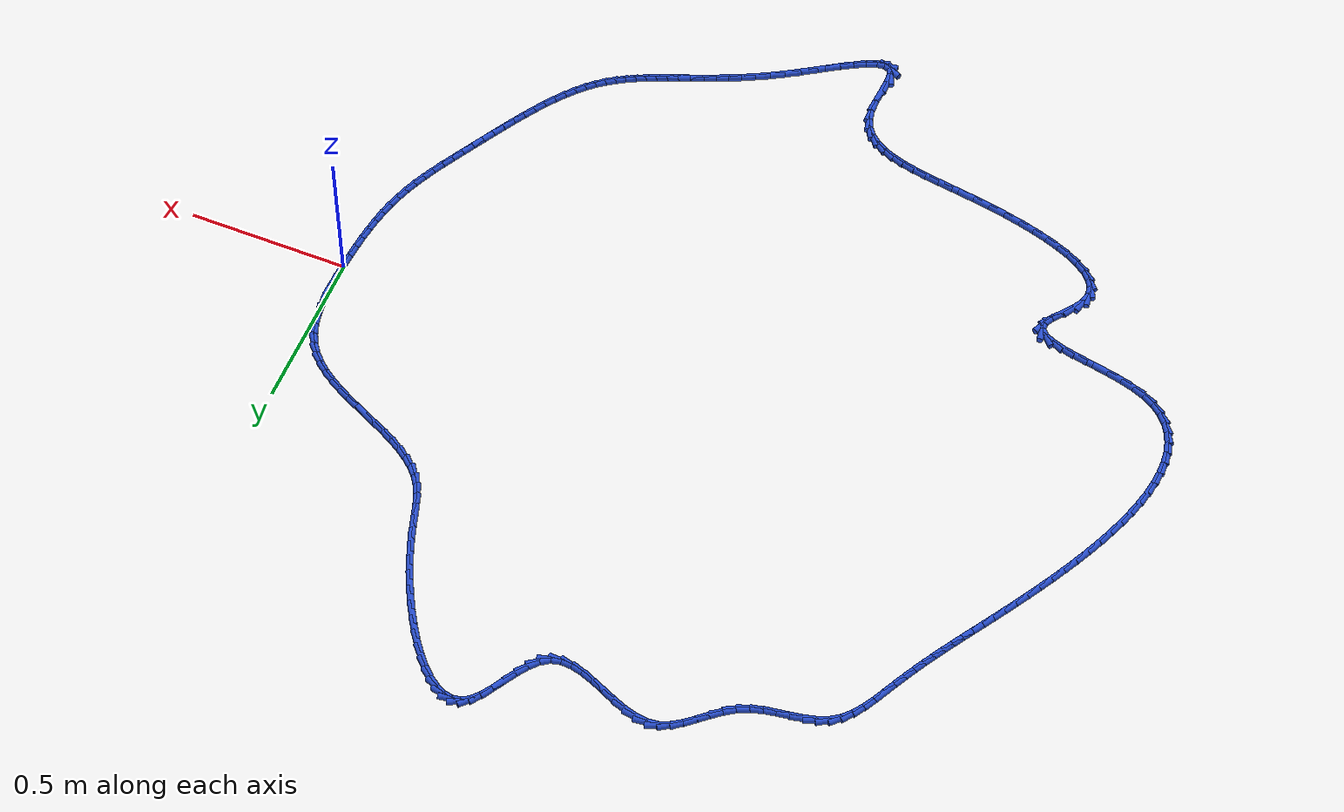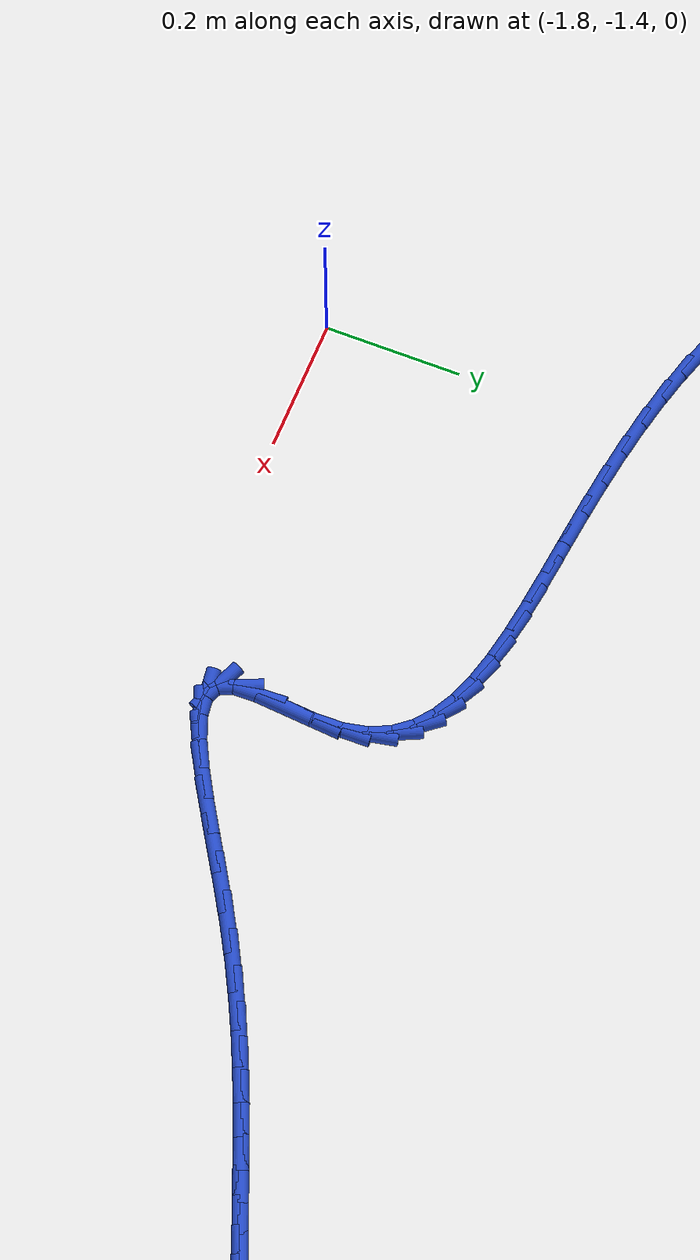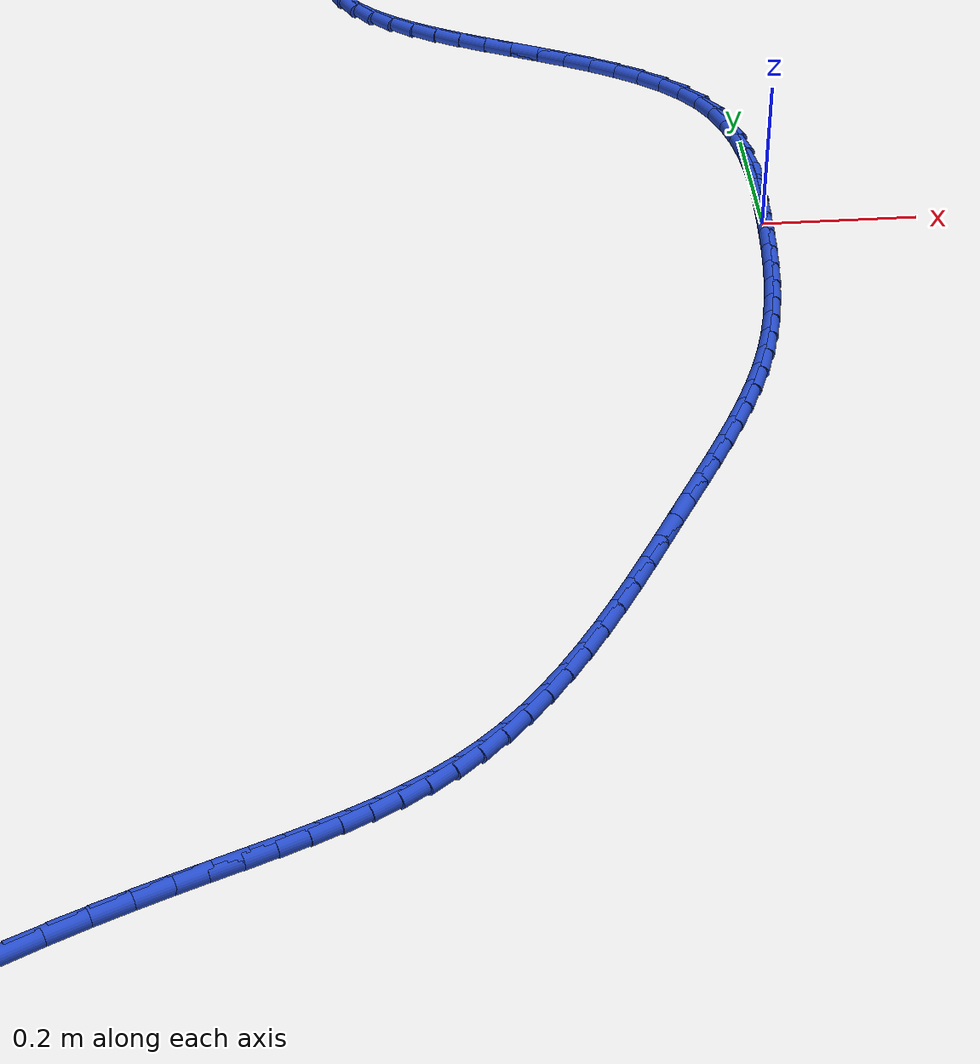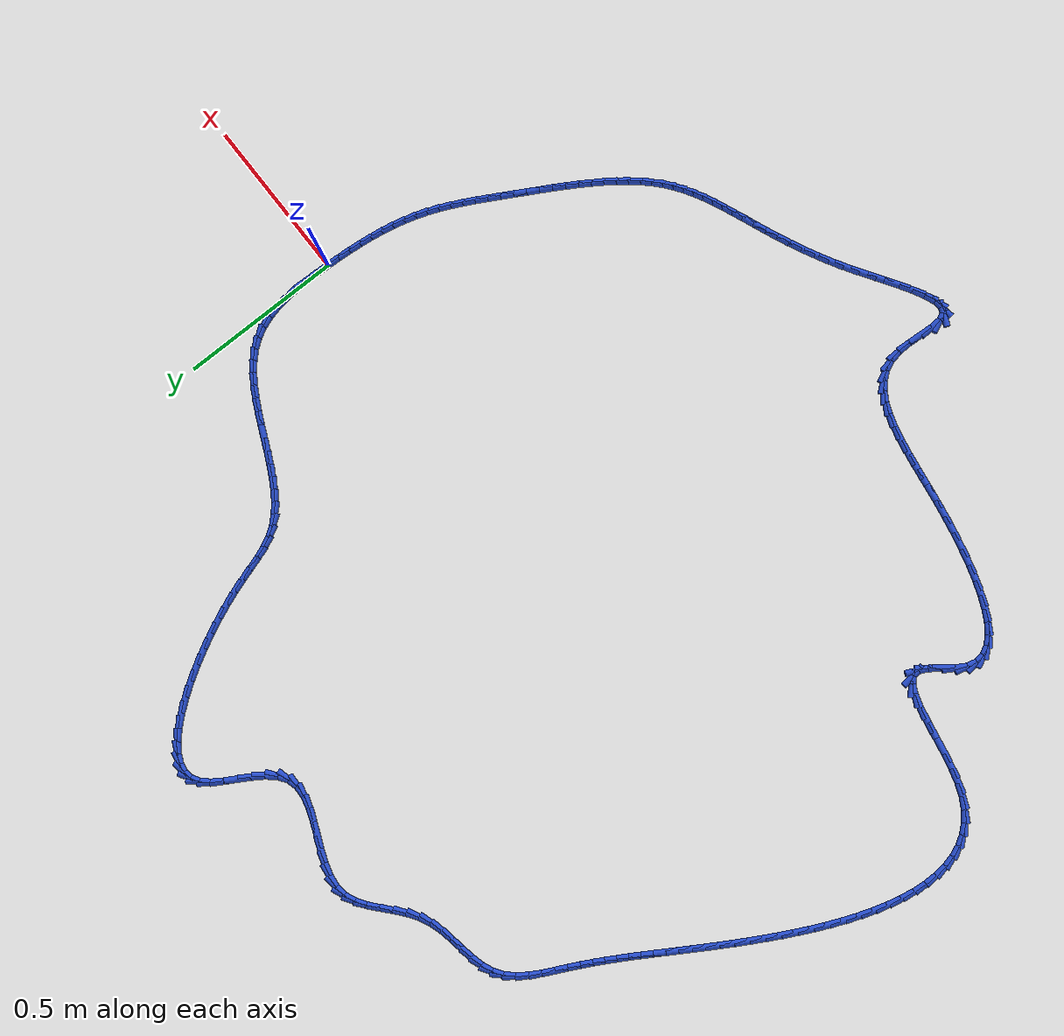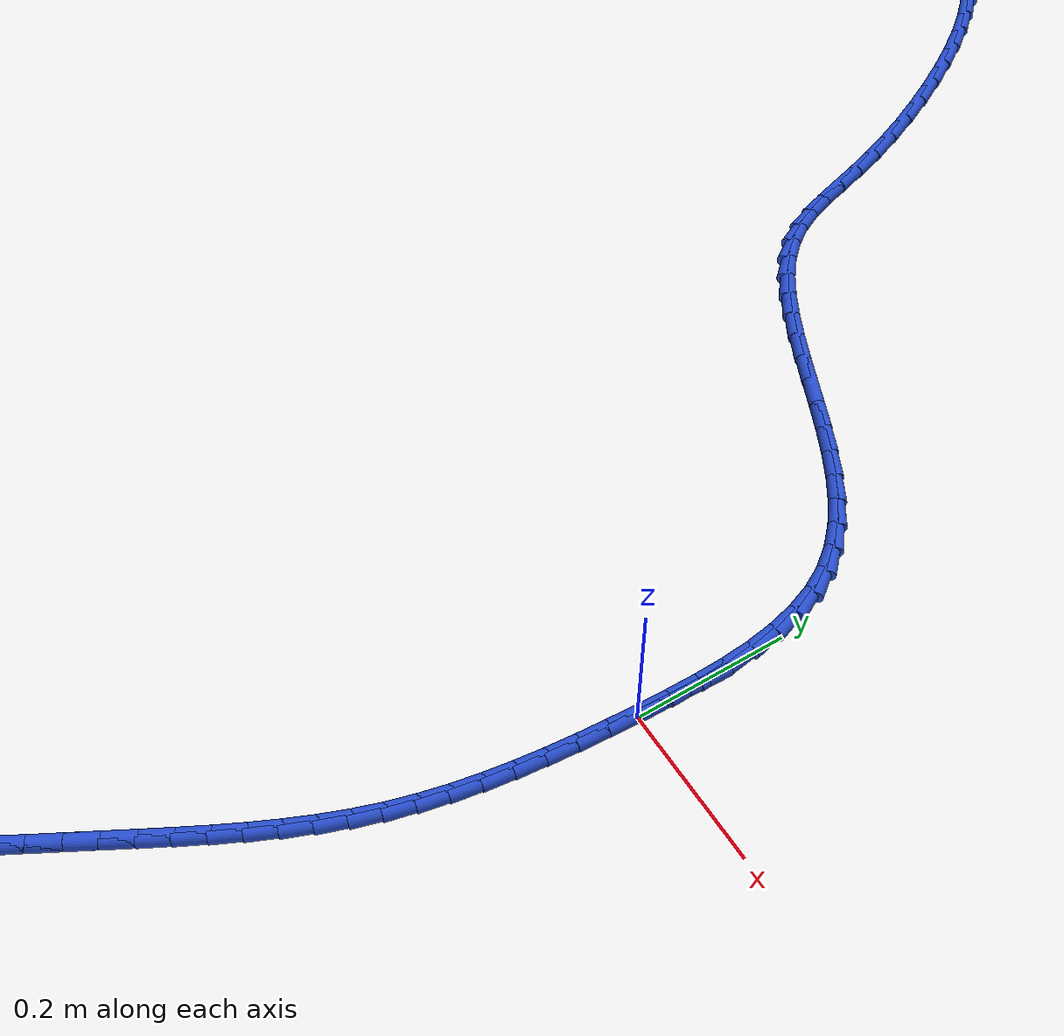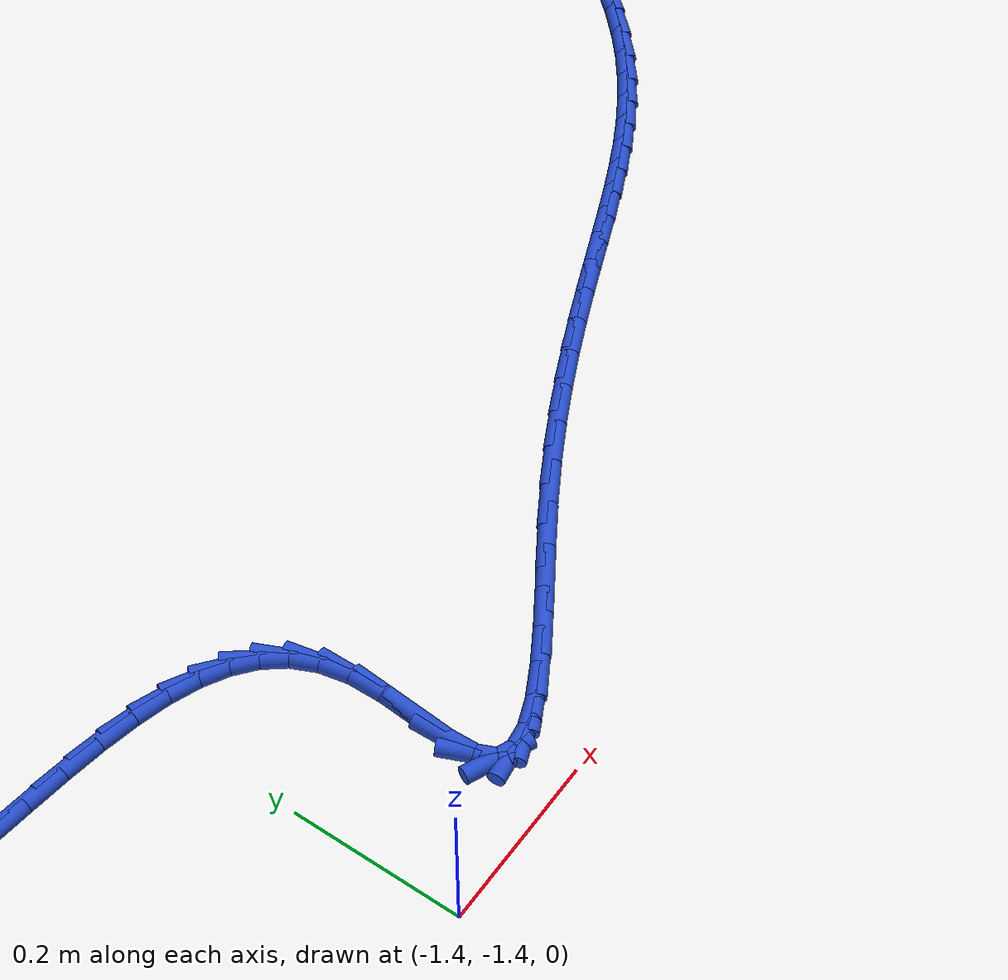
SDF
<sdf version="1.6">
 <world name="default">
  <light name="sun" type="directional">
   <pose>0 0 10 0 -0 0</pose>
   <diffuse>0.8 0.8 0.8 1</diffuse>
   <specular>0.2 0.2 0.2 1</specular>
   <attenuation>
    <range>1000</range>
    <constant>0.9</constant>
    <linear>0.01</linear>
    <quadratic>0.001</quadratic>
   </attenuation>
   <direction>-0.5 0.1 -0.9</direction>
  </light>
  <model name="ground_plane">
   <static>1</static>
   <link name="link">
    <collision name="collision">
     <geometry><plane><normal>0 0 1</normal><size>100 100</size></plane></geometry>
     <surface><friction><ode><mu>100</mu><mu2>50</mu2></ode></friction></surface>
    </collision>
    <visual name="visual">
     <cast_shadows>0</cast_shadows>
     <geometry><plane><normal>0 0 1</normal><size>100 100</size></plane></geometry>
     <material>
      <script><uri>file://media/materials/scripts/gazebo.material</uri><name>Gazebo/WhiteGlow</name></script>
     </material>
    </visual>
   </link>
  </model>
  <gravity>0 0 -9.8</gravity>
  <magnetic_field>6e-06 2.3e-05 -4.2e-05</magnetic_field>
  <atmosphere type="adiabatic"/>
  <physics name="default_physics" default="0" type="ode">
   <max_step_size>0.001</max_step_size>
   <real_time_factor>1</real_time_factor>
   <real_time_update_rate>1000</real_time_update_rate>
  </physics>
  <scene><ambient>0.4 0.4 0.4 1</ambient><background>0.7 0.7 0.7 1</background><shadows>1</shadows></scene>
  <spherical_coordinates>
   <surface_model>EARTH_WGS84</surface_model>
   <latitude_deg>0</latitude_deg>
   <longitude_deg>0</longitude_deg>
   <elevation>0</elevation>
   <heading_deg>0</heading_deg>
  </spherical_coordinates>
  <model name="line">
   <link name="link_0">
    <pose>3.350184712980209e-17 3.469446951953614e-17 0.01 0 1.57 1.5304056924930138</pose>
    <collision name="collision">
     <geometry><cylinder><radius>0.01</radius><length>0.08</length></cylinder></geometry>
    </collision>
    <visual name="visual">
     <material>
      <script><name>Gazebo/Blue</name><uri>file://media/materials/scripts/gazebo.material</uri></script>
     </material>
     <geometry><cylinder><radius>0.01</radius><length>0.08</length></cylinder></geometry>
    </visual>
   </link>
   <link name="link_1">
    <pose>0.001588194229673774 0.03929946883411981 0.01 0 1.57 1.5548960677146382</pose>
    <collision name="collision">
     <geometry><cylinder><radius>0.01</radius><length>0.08</length></cylinder></geometry>
    </collision>
    <visual name="visual">
     <material>
      <script><name>Gazebo/Blue</name><uri>file://media/materials/scripts/gazebo.material</uri></script>
     </material>
     <geometry><cylinder><radius>0.01</radius><length>0.08</length></cylinder></geometry>
    </visual>
   </link>
   <link name="link_2">
    <pose>0.002215800591229699 0.07876759745926659 0.01 0 1.57 -1.5488991715096991</pose>
    <collision name="collision">
     <geometry><cylinder><radius>0.01</radius><length>0.08</length></cylinder></geometry>
    </collision>
    <visual name="visual">
     <material>
      <script><name>Gazebo/Blue</name><uri>file://media/materials/scripts/gazebo.material</uri></script>
     </material>
     <geometry><cylinder><radius>0.01</radius><length>0.08</length></cylinder></geometry>
    </visual>
   </link>
   <link name="link_3">
    <pose>0.001357774036339202 0.11794571910391621 0.01 0 1.57 -1.496285921735271</pose>
    <collision name="collision">
     <geometry><cylinder><radius>0.01</radius><length>0.08</length></cylinder></geometry>
    </collision>
    <visual name="visual">
     <material>
      <script><name>Gazebo/Blue</name><uri>file://media/materials/scripts/gazebo.material</uri></script>
     </material>
     <geometry><cylinder><radius>0.01</radius><length>0.08</length></cylinder></geometry>
    </visual>
   </link>
   <link name="link_4">
    <pose>-0.001510930483326317 0.1563751669965446 0.01 0 1.57 -1.426609882147725</pose>
    <collision name="collision">
     <geometry><cylinder><radius>0.01</radius><length>0.08</length></cylinder></geometry>
    </collision>
    <visual name="visual">
     <material>
      <script><name>Gazebo/Blue</name><uri>file://media/materials/scripts/gazebo.material</uri></script>
     </material>
     <geometry><cylinder><radius>0.01</radius><length>0.08</length></cylinder></geometry>
    </visual>
   </link>
   <link name="link_5">
    <pose>-0.006915358016095463 0.19359727436562785 0.01 0 1.57 -1.3370675855114622</pose>
    <collision name="collision">
     <geometry><cylinder><radius>0.01</radius><length>0.08</length></cylinder></geometry>
    </collision>
    <visual name="visual">
     <material>
      <script><name>Gazebo/Blue</name><uri>file://media/materials/scripts/gazebo.material</uri></script>
     </material>
     <geometry><cylinder><radius>0.01</radius><length>0.08</length></cylinder></geometry>
    </visual>
   </link>
   <link name="link_6">
    <pose>-0.015380553610296843 0.22915337443964182 0.01 0 1.57 -1.2248251934461607</pose>
    <collision name="collision">
     <geometry><cylinder><radius>0.01</radius><length>0.08</length></cylinder></geometry>
    </collision>
    <visual name="visual">
     <material>
      <script><name>Gazebo/Blue</name><uri>file://media/materials/scripts/gazebo.material</uri></script>
     </material>
     <geometry><cylinder><radius>0.01</radius><length>0.08</length></cylinder></geometry>
    </visual>
   </link>
   <link name="link_7">
    <pose>-0.02743156231425906 0.26258480044706234 0.01 0 1.57 -1.0881979202606518</pose>
    <collision name="collision">
     <geometry><cylinder><radius>0.01</radius><length>0.08</length></cylinder></geometry>
    </collision>
    <visual name="visual">
     <material>
      <script><name>Gazebo/Blue</name><uri>file://media/materials/scripts/gazebo.material</uri></script>
     </material>
     <geometry><cylinder><radius>0.01</radius><length>0.08</length></cylinder></geometry>
    </visual>
   </link>
   <link name="link_8">
    <pose>-0.04359342917631069 0.2934328856163655 0.01 0 1.57 -0.9344725617930717</pose>
    <collision name="collision">
     <geometry><cylinder><radius>0.01</radius><length>0.08</length></cylinder></geometry>
    </collision>
    <visual name="visual">
     <material>
      <script><name>Gazebo/Blue</name><uri>file://media/materials/scripts/gazebo.material</uri></script>
     </material>
     <geometry><cylinder><radius>0.01</radius><length>0.08</length></cylinder></geometry>
    </visual>
   </link>
   <link name="link_9">
    <pose>-0.06422778586034152 0.3213607318713422 0.01 0 1.57 -0.7955751249455797</pose>
    <collision name="collision">
     <geometry><cylinder><radius>0.01</radius><length>0.08</length></cylinder></geometry>
    </collision>
    <visual name="visual">
     <material>
      <script><name>Gazebo/Blue</name><uri>file://media/materials/scripts/gazebo.material</uri></script>
     </material>
     <geometry><cylinder><radius>0.01</radius><length>0.08</length></cylinder></geometry>
    </visual>
   </link>
   <link name="link_10">
    <pose>-0.0889478444422824 0.3465891315421524 0.01 0 1.57 -0.6821644141039905</pose>
    <collision name="collision">
     <geometry><cylinder><radius>0.01</radius><length>0.08</length></cylinder></geometry>
    </collision>
    <visual name="visual">
     <material>
      <script><name>Gazebo/Blue</name><uri>file://media/materials/scripts/gazebo.material</uri></script>
     </material>
     <geometry><cylinder><radius>0.01</radius><length>0.08</length></cylinder></geometry>
    </visual>
   </link>
   <link name="link_11">
    <pose>-0.11715268341810359 0.3694984401841134 0.01 0 1.57 -0.593434187609674</pose>
    <collision name="collision">
     <geometry><cylinder><radius>0.01</radius><length>0.08</length></cylinder></geometry>
    </collision>
    <visual name="visual">
     <material>
      <script><name>Gazebo/Blue</name><uri>file://media/materials/scripts/gazebo.material</uri></script>
     </material>
     <geometry><cylinder><radius>0.01</radius><length>0.08</length></cylinder></geometry>
    </visual>
   </link>
   <link name="link_12">
    <pose>-0.1482413640963834 0.3904690261598552 0.01 0 1.57 -0.5268545136994857</pose>
    <collision name="collision">
     <geometry><cylinder><radius>0.01</radius><length>0.08</length></cylinder></geometry>
    </collision>
    <visual name="visual">
     <material>
      <script><name>Gazebo/Blue</name><uri>file://media/materials/scripts/gazebo.material</uri></script>
     </material>
     <geometry><cylinder><radius>0.01</radius><length>0.08</length></cylinder></geometry>
    </visual>
   </link>
   <link name="link_13">
    <pose>-0.1816129477857002 0.4098812578320075 0.01 0 1.57 -0.4796630152522517</pose>
    <collision name="collision">
     <geometry><cylinder><radius>0.01</radius><length>0.08</length></cylinder></geometry>
    </collision>
    <visual name="visual">
     <material>
      <script><name>Gazebo/Blue</name><uri>file://media/materials/scripts/gazebo.material</uri></script>
     </material>
     <geometry><cylinder><radius>0.01</radius><length>0.08</length></cylinder></geometry>
    </visual>
   </link>
   <link name="link_14">
    <pose>-0.2166664957946325 0.42811550356320033 0.01 0 1.57 -0.4495879320825388</pose>
    <collision name="collision">
     <geometry><cylinder><radius>0.01</radius><length>0.08</length></cylinder></geometry>
    </collision>
    <visual name="visual">
     <material>
      <script><name>Gazebo/Blue</name><uri>file://media/materials/scripts/gazebo.material</uri></script>
     </material>
     <geometry><cylinder><radius>0.01</radius><length>0.08</length></cylinder></geometry>
    </visual>
   </link>
   <link name="link_15">
    <pose>-0.2528010694317585 0.4455521317160631 0.01 0 1.57 -0.4351130866983089</pose>
    <collision name="collision">
     <geometry><cylinder><radius>0.01</radius><length>0.08</length></cylinder></geometry>
    </collision>
    <visual name="visual">
     <material>
      <script><name>Gazebo/Blue</name><uri>file://media/materials/scripts/gazebo.material</uri></script>
     </material>
     <geometry><cylinder><radius>0.01</radius><length>0.08</length></cylinder></geometry>
    </visual>
   </link>
   <link name="link_16">
    <pose>-0.2894157300056566 0.46257151065322594 0.01 0 1.57 -0.435547755946695</pose>
    <collision name="collision">
     <geometry><cylinder><radius>0.01</radius><length>0.08</length></cylinder></geometry>
    </collision>
    <visual name="visual">
     <material>
      <script><name>Gazebo/Blue</name><uri>file://media/materials/scripts/gazebo.material</uri></script>
     </material>
     <geometry><cylinder><radius>0.01</radius><length>0.08</length></cylinder></geometry>
    </visual>
   </link>
   <link name="link_17">
    <pose>-0.32590953882490536 0.47955400873731874 0.01 0 1.57 -0.4510450703834946</pose>
    <collision name="collision">
     <geometry><cylinder><radius>0.01</radius><length>0.08</length></cylinder></geometry>
    </collision>
    <visual name="visual">
     <material>
      <script><name>Gazebo/Blue</name><uri>file://media/materials/scripts/gazebo.material</uri></script>
     </material>
     <geometry><cylinder><radius>0.01</radius><length>0.08</length></cylinder></geometry>
    </visual>
   </link>
   <link name="link_18">
    <pose>-0.361681557198083 0.4968799943309711 0.01 0 1.57 -0.48262662591067285</pose>
    <collision name="collision">
     <geometry><cylinder><radius>0.01</radius><length>0.08</length></cylinder></geometry>
    </collision>
    <visual name="visual">
     <material>
      <script><name>Gazebo/Blue</name><uri>file://media/materials/scripts/gazebo.material</uri></script>
     </material>
     <geometry><cylinder><radius>0.01</radius><length>0.08</length></cylinder></geometry>
    </visual>
   </link>
   <link name="link_19">
    <pose>-0.396130846433768 0.5149298357968131 0.01 0 1.57 -0.5322115278446409</pose>
    <collision name="collision">
     <geometry><cylinder><radius>0.01</radius><length>0.08</length></cylinder></geometry>
    </collision>
    <visual name="visual">
     <material>
      <script><name>Gazebo/Blue</name><uri>file://media/materials/scripts/gazebo.material</uri></script>
     </material>
     <geometry><cylinder><radius>0.01</radius><length>0.08</length></cylinder></geometry>
    </visual>
   </link>
   <link name="link_20">
    <pose>-0.4286564678405386 0.5340839014974743 0.01 0 1.57 -0.6025806372912285</pose>
    <collision name="collision">
     <geometry><cylinder><radius>0.01</radius><length>0.08</length></cylinder></geometry>
    </collision>
    <visual name="visual">
     <material>
      <script><name>Gazebo/Blue</name><uri>file://media/materials/scripts/gazebo.material</uri></script>
     </material>
     <geometry><cylinder><radius>0.01</radius><length>0.08</length></cylinder></geometry>
    </visual>
   </link>
   <link name="link_21">
    <pose>-0.4586574827269732 0.5547225597955846 0.01 0 1.57 -0.6970919447280229</pose>
    <collision name="collision">
     <geometry><cylinder><radius>0.01</radius><length>0.08</length></cylinder></geometry>
    </collision>
    <visual name="visual">
     <material>
      <script><name>Gazebo/Blue</name><uri>file://media/materials/scripts/gazebo.material</uri></script>
     </material>
     <geometry><cylinder><radius>0.01</radius><length>0.08</length></cylinder></geometry>
    </visual>
   </link>
   <link name="link_22">
    <pose>-0.48553295240165034 0.5772261790537738 0.01 0 1.57 -0.8187893346411759</pose>
    <collision name="collision">
     <geometry><cylinder><radius>0.01</radius><length>0.08</length></cylinder></geometry>
    </collision>
    <visual name="visual">
     <material>
      <script><name>Gazebo/Blue</name><uri>file://media/materials/scripts/gazebo.material</uri></script>
     </material>
     <geometry><cylinder><radius>0.01</radius><length>0.08</length></cylinder></geometry>
    </visual>
   </link>
   <link name="link_23">
    <pose>-0.5086819381731484 0.6019751276346721 0.01 0 1.57 -0.9670127684586959</pose>
    <collision name="collision">
     <geometry><cylinder><radius>0.01</radius><length>0.08</length></cylinder></geometry>
    </collision>
    <visual name="visual">
     <material>
      <script><name>Gazebo/Blue</name><uri>file://media/materials/scripts/gazebo.material</uri></script>
     </material>
     <geometry><cylinder><radius>0.01</radius><length>0.08</length></cylinder></geometry>
    </visual>
   </link>
   <link name="link_24">
    <pose>-0.5275546866714497 0.6293386090940043 0.01 0 1.57 -1.1075245304353976</pose>
    <collision name="collision">
     <geometry><cylinder><radius>0.01</radius><length>0.08</length></cylinder></geometry>
    </collision>
    <visual name="visual">
     <material>
      <script><name>Gazebo/Blue</name><uri>file://media/materials/scripts/gazebo.material</uri></script>
     </material>
     <geometry><cylinder><radius>0.01</radius><length>0.08</length></cylinder></geometry>
    </visual>
   </link>
   <link name="link_25">
    <pose>-0.5426047246696288 0.6594669863362863 0.01 0 1.57 -1.2045844939877883</pose>
    <collision name="collision">
     <geometry><cylinder><radius>0.01</radius><length>0.08</length></cylinder></geometry>
    </collision>
    <visual name="visual">
     <material>
      <script><name>Gazebo/Blue</name><uri>file://media/materials/scripts/gazebo.material</uri></script>
     </material>
     <geometry><cylinder><radius>0.01</radius><length>0.08</length></cylinder></geometry>
    </visual>
   </link>
   <link name="link_26">
    <pose>-0.5552007788361379 0.6923109941337802 0.01 0 1.57 -1.2564160436212048</pose>
    <collision name="collision">
     <geometry><cylinder><radius>0.01</radius><length>0.08</length></cylinder></geometry>
    </collision>
    <visual name="visual">
     <material>
      <script><name>Gazebo/Blue</name><uri>file://media/materials/scripts/gazebo.material</uri></script>
     </material>
     <geometry><cylinder><radius>0.01</radius><length>0.08</length></cylinder></geometry>
    </visual>
   </link>
   <link name="link_27">
    <pose>-0.5667450984718043 0.7278140551288811 0.01 0 1.57 -1.2682257820648055</pose>
    <collision name="collision">
     <geometry><cylinder><radius>0.01</radius><length>0.08</length></cylinder></geometry>
    </collision>
    <visual name="visual">
     <material>
      <script><name>Gazebo/Blue</name><uri>file://media/materials/scripts/gazebo.material</uri></script>
     </material>
     <geometry><cylinder><radius>0.01</radius><length>0.08</length></cylinder></geometry>
    </visual>
   </link>
   <link name="link_28">
    <pose>-0.578639932877455 0.7659195919639842 0.01 0 1.57 -1.246910897992243</pose>
    <collision name="collision">
     <geometry><cylinder><radius>0.01</radius><length>0.08</length></cylinder></geometry>
    </collision>
    <visual name="visual">
     <material>
      <script><name>Gazebo/Blue</name><uri>file://media/materials/scripts/gazebo.material</uri></script>
     </material>
     <geometry><cylinder><radius>0.01</radius><length>0.08</length></cylinder></geometry>
    </visual>
   </link>
   <link name="link_29">
    <pose>-0.592286793812349 0.8065706850600511 0.01 0 1.57 -1.206390463391345</pose>
    <collision name="collision">
     <geometry><cylinder><radius>0.01</radius><length>0.08</length></cylinder></geometry>
    </collision>
    <visual name="visual">
     <material>
      <script><name>Gazebo/Blue</name><uri>file://media/materials/scripts/gazebo.material</uri></script>
     </material>
     <geometry><cylinder><radius>0.01</radius><length>0.08</length></cylinder></geometry>
    </visual>
   </link>
   <link name="link_30">
    <pose>-0.6086678498791283 0.8495158383934366 0.01 0 1.57 -1.1674212371771375</pose>
    <collision name="collision">
     <geometry><cylinder><radius>0.01</radius><length>0.08</length></cylinder></geometry>
    </collision>
    <visual name="visual">
     <material>
      <script><name>Gazebo/Blue</name><uri>file://media/materials/scripts/gazebo.material</uri></script>
     </material>
     <geometry><cylinder><radius>0.01</radius><length>0.08</length></cylinder></geometry>
    </visual>
   </link>
   <link name="link_31">
    <pose>-0.6276459289143288 0.8939841785686773 0.01 0 1.57 -1.1307141311978097</pose>
    <collision name="collision">
     <geometry><cylinder><radius>0.01</radius><length>0.08</length></cylinder></geometry>
    </collision>
    <visual name="visual">
     <material>
      <script><name>Gazebo/Blue</name><uri>file://media/materials/scripts/gazebo.material</uri></script>
     </material>
     <geometry><cylinder><radius>0.01</radius><length>0.08</length></cylinder></geometry>
    </visual>
   </link>
   <link name="link_32">
    <pose>-0.6488991064256552 0.9391191065722582 0.01 0 1.57 -1.0941712352187705</pose>
    <collision name="collision">
     <geometry><cylinder><radius>0.01</radius><length>0.08</length></cylinder></geometry>
    </collision>
    <visual name="visual">
     <material>
      <script><name>Gazebo/Blue</name><uri>file://media/materials/scripts/gazebo.material</uri></script>
     </material>
     <geometry><cylinder><radius>0.01</radius><length>0.08</length></cylinder></geometry>
    </visual>
   </link>
   <link name="link_33">
    <pose>-0.672105457920811 0.9840640233906636 0.01 0 1.57 -1.055904627514674</pose>
    <collision name="collision">
     <geometry><cylinder><radius>0.01</radius><length>0.08</length></cylinder></geometry>
    </collision>
    <visual name="visual">
     <material>
      <script><name>Gazebo/Blue</name><uri>file://media/materials/scripts/gazebo.material</uri></script>
     </material>
     <geometry><cylinder><radius>0.01</radius><length>0.08</length></cylinder></geometry>
    </visual>
   </link>
   <link name="link_34">
    <pose>-0.6969430589075 1.0279623300103768 0.01 0 1.57 -1.0139113595048148</pose>
    <collision name="collision">
     <geometry><cylinder><radius>0.01</radius><length>0.08</length></cylinder></geometry>
    </collision>
    <visual name="visual">
     <material>
      <script><name>Gazebo/Blue</name><uri>file://media/materials/scripts/gazebo.material</uri></script>
     </material>
     <geometry><cylinder><radius>0.01</radius><length>0.08</length></cylinder></geometry>
    </visual>
   </link>
   <link name="link_35">
    <pose>-0.7230899848934266 1.0699574274178836 0.01 0 1.57 -0.9657440058951108</pose>
    <collision name="collision">
     <geometry><cylinder><radius>0.01</radius><length>0.08</length></cylinder></geometry>
    </collision>
    <visual name="visual">
     <material>
      <script><name>Gazebo/Blue</name><uri>file://media/materials/scripts/gazebo.material</uri></script>
     </material>
     <geometry><cylinder><radius>0.01</radius><length>0.08</length></cylinder></geometry>
    </visual>
   </link>
   <link name="link_36">
    <pose>-0.7502243113862943 1.1091927165996673 0.01 0 1.57 -0.9080720612517078</pose>
    <collision name="collision">
     <geometry><cylinder><radius>0.01</radius><length>0.08</length></cylinder></geometry>
    </collision>
    <visual name="visual">
     <material>
      <script><name>Gazebo/Blue</name><uri>file://media/materials/scripts/gazebo.material</uri></script>
     </material>
     <geometry><cylinder><radius>0.01</radius><length>0.08</length></cylinder></geometry>
    </visual>
   </link>
   <link name="link_37">
    <pose>-0.7780241138938074 1.1448115985422136 0.01 0 1.57 -0.8359968784538038</pose>
    <collision name="collision">
     <geometry><cylinder><radius>0.01</radius><length>0.08</length></cylinder></geometry>
    </collision>
    <visual name="visual">
     <material>
      <script><name>Gazebo/Blue</name><uri>file://media/materials/scripts/gazebo.material</uri></script>
     </material>
     <geometry><cylinder><radius>0.01</radius><length>0.08</length></cylinder></geometry>
    </visual>
   </link>
   <link name="link_38">
    <pose>-0.8061674679236698 1.1759574742320058 0.01 0 1.57 -0.7419158405569487</pose>
    <collision name="collision">
     <geometry><cylinder><radius>0.01</radius><length>0.08</length></cylinder></geometry>
    </collision>
    <visual name="visual">
     <material>
      <script><name>Gazebo/Blue</name><uri>file://media/materials/scripts/gazebo.material</uri></script>
     </material>
     <geometry><cylinder><radius>0.01</radius><length>0.08</length></cylinder></geometry>
    </visual>
   </link>
   <link name="link_39">
    <pose>-0.834332448983585 1.201773744655528 0.01 0 1.57 -0.6137252448125574</pose>
    <collision name="collision">
     <geometry><cylinder><radius>0.01</radius><length>0.08</length></cylinder></geometry>
    </collision>
    <visual name="visual">
     <material>
      <script><name>Gazebo/Blue</name><uri>file://media/materials/scripts/gazebo.material</uri></script>
     </material>
     <geometry><cylinder><radius>0.01</radius><length>0.08</length></cylinder></geometry>
    </visual>
   </link>
   <link name="link_40">
    <pose>-0.8621971325812576 1.2214038107992655 0.01 0 1.57 -0.43282587516805054</pose>
    <collision name="collision">
     <geometry><cylinder><radius>0.01</radius><length>0.08</length></cylinder></geometry>
    </collision>
    <visual name="visual">
     <material>
      <script><name>Gazebo/Blue</name><uri>file://media/materials/scripts/gazebo.material</uri></script>
     </material>
     <geometry><cylinder><radius>0.01</radius><length>0.08</length></cylinder></geometry>
    </visual>
   </link>
   <link name="link_41">
    <pose>-0.8894395942243916 1.233991073649703 0.01 0 1.57 -0.17640419280180014</pose>
    <collision name="collision">
     <geometry><cylinder><radius>0.01</radius><length>0.08</length></cylinder></geometry>
    </collision>
    <visual name="visual">
     <material>
      <script><name>Gazebo/Blue</name><uri>file://media/materials/scripts/gazebo.material</uri></script>
     </material>
     <geometry><cylinder><radius>0.01</radius><length>0.08</length></cylinder></geometry>
    </visual>
   </link>
   <link name="link_42">
    <pose>-0.9157379094206898 1.2386789341933233 0.01 0 1.57 0.16110751501398704</pose>
    <collision name="collision">
     <geometry><cylinder><radius>0.01</radius><length>0.08</length></cylinder></geometry>
    </collision>
    <visual name="visual">
     <material>
      <script><name>Gazebo/Blue</name><uri>file://media/materials/scripts/gazebo.material</uri></script>
     </material>
     <geometry><cylinder><radius>0.01</radius><length>0.08</length></cylinder></geometry>
    </visual>
   </link>
   <link name="link_43">
    <pose>-0.9407701536778574 1.2346107934166126 0.01 0 1.57 0.5282313090634218</pose>
    <collision name="collision">
     <geometry><cylinder><radius>0.01</radius><length>0.08</length></cylinder></geometry>
    </collision>
    <visual name="visual">
     <material>
      <script><name>Gazebo/Blue</name><uri>file://media/materials/scripts/gazebo.material</uri></script>
     </material>
     <geometry><cylinder><radius>0.01</radius><length>0.08</length></cylinder></geometry>
    </visual>
   </link>
   <link name="link_44">
    <pose>-0.9642144025035979 1.2209300523060538 0.01 0 1.57 0.8261475906959247</pose>
    <collision name="collision">
     <geometry><cylinder><radius>0.01</radius><length>0.08</length></cylinder></geometry>
    </collision>
    <visual name="visual">
     <material>
      <script><name>Gazebo/Blue</name><uri>file://media/materials/scripts/gazebo.material</uri></script>
     </material>
     <geometry><cylinder><radius>0.01</radius><length>0.08</length></cylinder></geometry>
    </visual>
   </link>
   <link name="link_45">
    <pose>-0.9859157041550654 1.1973839225008271 0.01 0 1.57 0.9838684503298167</pose>
    <collision name="collision">
     <geometry><cylinder><radius>0.01</radius><length>0.08</length></cylinder></geometry>
    </collision>
    <visual name="visual">
     <material>
      <script><name>Gazebo/Blue</name><uri>file://media/materials/scripts/gazebo.material</uri></script>
     </material>
     <geometry><cylinder><radius>0.01</radius><length>0.08</length></cylinder></geometry>
    </visual>
   </link>
   <link name="link_46">
    <pose>-1.0064788983484243 1.1664671907880781 0.01 0 1.57 1.046511109402985</pose>
    <collision name="collision">
     <geometry><cylinder><radius>0.01</radius><length>0.08</length></cylinder></geometry>
    </collision>
    <visual name="visual">
     <material>
      <script><name>Gazebo/Blue</name><uri>file://media/materials/scripts/gazebo.material</uri></script>
     </material>
     <geometry><cylinder><radius>0.01</radius><length>0.08</length></cylinder></geometry>
    </visual>
   </link>
   <link name="link_47">
    <pose>-1.0267248236877158 1.1314557440440376 0.01 0 1.57 1.0458814504760674</pose>
    <collision name="collision">
     <geometry><cylinder><radius>0.01</radius><length>0.08</length></cylinder></geometry>
    </collision>
    <visual name="visual">
     <material>
      <script><name>Gazebo/Blue</name><uri>file://media/materials/scripts/gazebo.material</uri></script>
     </material>
     <geometry><cylinder><radius>0.01</radius><length>0.08</length></cylinder></geometry>
    </visual>
   </link>
   <link name="link_48">
    <pose>-1.0474743338433463 1.0956255236282668 0.01 0 1.57 0.9864276590710491</pose>
    <collision name="collision">
     <geometry><cylinder><radius>0.01</radius><length>0.08</length></cylinder></geometry>
    </collision>
    <visual name="visual">
     <material>
      <script><name>Gazebo/Blue</name><uri>file://media/materials/scripts/gazebo.material</uri></script>
     </material>
     <geometry><cylinder><radius>0.01</radius><length>0.08</length></cylinder></geometry>
    </visual>
   </link>
   <link name="link_49">
    <pose>-1.0695482824857214 1.0622524709003276 0.01 0 1.57 0.8512641190242259</pose>
    <collision name="collision">
     <geometry><cylinder><radius>0.01</radius><length>0.08</length></cylinder></geometry>
    </collision>
    <visual name="visual">
     <material>
      <script><name>Gazebo/Blue</name><uri>file://media/materials/scripts/gazebo.material</uri></script>
     </material>
     <geometry><cylinder><radius>0.01</radius><length>0.08</length></cylinder></geometry>
    </visual>
   </link>
   <link name="link_50">
    <pose>-1.093767523285248 1.0346125272197821 0.01 0 1.57 0.6008503914331939</pose>
    <collision name="collision">
     <geometry><cylinder><radius>0.01</radius><length>0.08</length></cylinder></geometry>
    </collision>
    <visual name="visual">
     <material>
      <script><name>Gazebo/Blue</name><uri>file://media/materials/scripts/gazebo.material</uri></script>
     </material>
     <geometry><cylinder><radius>0.01</radius><length>0.08</length></cylinder></geometry>
    </visual>
   </link>
   <link name="link_51">
    <pose>-1.1209525520797299 1.015980290523162 0.01 0 1.57 0.24369115881245274</pose>
    <collision name="collision">
     <geometry><cylinder><radius>0.01</radius><length>0.08</length></cylinder></geometry>
    </collision>
    <visual name="visual">
     <material>
      <script><name>Gazebo/Blue</name><uri>file://media/materials/scripts/gazebo.material</uri></script>
     </material>
     <geometry><cylinder><radius>0.01</radius><length>0.08</length></cylinder></geometry>
    </visual>
   </link>
   <link name="link_52">
    <pose>-1.151586479385366 1.0083637016312395 0.01 0 1.57 -0.05314590008722876</pose>
    <collision name="collision">
     <geometry><cylinder><radius>0.01</radius><length>0.08</length></cylinder></geometry>
    </collision>
    <visual name="visual">
     <material>
      <script><name>Gazebo/Blue</name><uri>file://media/materials/scripts/gazebo.material</uri></script>
     </material>
     <geometry><cylinder><radius>0.01</radius><length>0.08</length></cylinder></geometry>
    </visual>
   </link>
   <link name="link_53">
    <pose>-1.1851883255914524 1.0101511852172993 0.01 0 1.57 -0.24388330143926176</pose>
    <collision name="collision">
     <geometry><cylinder><radius>0.01</radius><length>0.08</length></cylinder></geometry>
    </collision>
    <visual name="visual">
     <material>
      <script><name>Gazebo/Blue</name><uri>file://media/materials/scripts/gazebo.material</uri></script>
     </material>
     <geometry><cylinder><radius>0.01</radius><length>0.08</length></cylinder></geometry>
    </visual>
   </link>
   <link name="link_54">
    <pose>-1.2211060158773202 1.0190888174252317 0.01 0 1.57 -0.35271052769358696</pose>
    <collision name="collision">
     <geometry><cylinder><radius>0.01</radius><length>0.08</length></cylinder></geometry>
    </collision>
    <visual name="visual">
     <material>
      <script><name>Gazebo/Blue</name><uri>file://media/materials/scripts/gazebo.material</uri></script>
     </material>
     <geometry><cylinder><radius>0.01</radius><length>0.08</length></cylinder></geometry>
    </visual>
   </link>
   <link name="link_55">
    <pose>-1.258687475422302 1.0329226743989293 0.01 0 1.57 -0.4034950915412203</pose>
    <collision name="collision">
     <geometry><cylinder><radius>0.01</radius><length>0.08</length></cylinder></geometry>
    </collision>
    <visual name="visual">
     <material>
      <script><name>Gazebo/Blue</name><uri>file://media/materials/scripts/gazebo.material</uri></script>
     </material>
     <geometry><cylinder><radius>0.01</radius><length>0.08</length></cylinder></geometry>
    </visual>
   </link>
   <link name="link_56">
    <pose>-1.2972806294057295 1.049398832282282 0.01 0 1.57 -0.40858357364994696</pose>
    <collision name="collision">
     <geometry><cylinder><radius>0.01</radius><length>0.08</length></cylinder></geometry>
    </collision>
    <visual name="visual">
     <material>
      <script><name>Gazebo/Blue</name><uri>file://media/materials/scripts/gazebo.material</uri></script>
     </material>
     <geometry><cylinder><radius>0.01</radius><length>0.08</length></cylinder></geometry>
    </visual>
   </link>
   <link name="link_57">
    <pose>-1.3362334030069343 1.0662633672191812 0.01 0 1.57 -0.3700916143112382</pose>
    <collision name="collision">
     <geometry><cylinder><radius>0.01</radius><length>0.08</length></cylinder></geometry>
    </collision>
    <visual name="visual">
     <material>
      <script><name>Gazebo/Blue</name><uri>file://media/materials/scripts/gazebo.material</uri></script>
     </material>
     <geometry><cylinder><radius>0.01</radius><length>0.08</length></cylinder></geometry>
    </visual>
   </link>
   <link name="link_58">
    <pose>-1.3748937214052492 1.081262355353518 0.01 0 1.57 -0.28083682230791335</pose>
    <collision name="collision">
     <geometry><cylinder><radius>0.01</radius><length>0.08</length></cylinder></geometry>
    </collision>
    <visual name="visual">
     <material>
      <script><name>Gazebo/Blue</name><uri>file://media/materials/scripts/gazebo.material</uri></script>
     </material>
     <geometry><cylinder><radius>0.01</radius><length>0.08</length></cylinder></geometry>
    </visual>
   </link>
   <link name="link_59">
    <pose>-1.412609509780005 1.0921418728291827 0.01 0 1.57 -0.12411577986707746</pose>
    <collision name="collision">
     <geometry><cylinder><radius>0.01</radius><length>0.08</length></cylinder></geometry>
    </collision>
    <visual name="visual">
     <material>
      <script><name>Gazebo/Blue</name><uri>file://media/materials/scripts/gazebo.material</uri></script>
     </material>
     <geometry><cylinder><radius>0.01</radius><length>0.08</length></cylinder></geometry>
    </visual>
   </link>
   <link name="link_60">
    <pose>-1.4487286933105357 1.0966479957900679 0.01 0 1.57 0.12006608974457447</pose>
    <collision name="collision">
     <geometry><cylinder><radius>0.01</radius><length>0.08</length></cylinder></geometry>
    </collision>
    <visual name="visual">
     <material>
      <script><name>Gazebo/Blue</name><uri>file://media/materials/scripts/gazebo.material</uri></script>
     </material>
     <geometry><cylinder><radius>0.01</radius><length>0.08</length></cylinder></geometry>
    </visual>
   </link>
   <link name="link_61">
    <pose>-1.4826096412727539 1.0925603817830614 0.01 0 1.57 0.39332218002669034</pose>
    <collision name="collision">
     <geometry><cylinder><radius>0.01</radius><length>0.08</length></cylinder></geometry>
    </collision>
    <visual name="visual">
     <material>
      <script><name>Gazebo/Blue</name><uri>file://media/materials/scripts/gazebo.material</uri></script>
     </material>
     <geometry><cylinder><radius>0.01</radius><length>0.08</length></cylinder></geometry>
    </visual>
   </link>
   <link name="link_62">
    <pose>-1.514172107097579 1.0794637336642297 0.01 0 1.57 0.5842710907141366</pose>
    <collision name="collision">
     <geometry><cylinder><radius>0.01</radius><length>0.08</length></cylinder></geometry>
    </collision>
    <visual name="visual">
     <material>
      <script><name>Gazebo/Blue</name><uri>file://media/materials/scripts/gazebo.material</uri></script>
     </material>
     <geometry><cylinder><radius>0.01</radius><length>0.08</length></cylinder></geometry>
    </visual>
   </link>
   <link name="link_63">
    <pose>-1.5441704050391432 1.05962615759866 0.01 0 1.57 0.688905536754991</pose>
    <collision name="collision">
     <geometry><cylinder><radius>0.01</radius><length>0.08</length></cylinder></geometry>
    </collision>
    <visual name="visual">
     <material>
      <script><name>Gazebo/Blue</name><uri>file://media/materials/scripts/gazebo.material</uri></script>
     </material>
     <geometry><cylinder><radius>0.01</radius><length>0.08</length></cylinder></geometry>
    </visual>
   </link>
   <link name="link_64">
    <pose>-1.5734266357706956 1.0355337166651923 0.01 0 1.57 0.7225250102376076</pose>
    <collision name="collision">
     <geometry><cylinder><radius>0.01</radius><length>0.08</length></cylinder></geometry>
    </collision>
    <visual name="visual">
     <material>
      <script><name>Gazebo/Blue</name><uri>file://media/materials/scripts/gazebo.material</uri></script>
     </material>
     <geometry><cylinder><radius>0.01</radius><length>0.08</length></cylinder></geometry>
    </visual>
   </link>
   <link name="link_65">
    <pose>-1.6027628999654866 1.0096724739426632 0.01 0 1.57 0.6936700599582344</pose>
    <collision name="collision">
     <geometry><cylinder><radius>0.01</radius><length>0.08</length></cylinder></geometry>
    </collision>
    <visual name="visual">
     <material>
      <script><name>Gazebo/Blue</name><uri>file://media/materials/scripts/gazebo.material</uri></script>
     </material>
     <geometry><cylinder><radius>0.01</radius><length>0.08</length></cylinder></geometry>
    </visual>
   </link>
   <link name="link_66">
    <pose>-1.633001298296764 0.9845284925099096 0.01 0 1.57 0.6015720330930103</pose>
    <collision name="collision">
     <geometry><cylinder><radius>0.01</radius><length>0.08</length></cylinder></geometry>
    </collision>
    <visual name="visual">
     <material>
      <script><name>Gazebo/Blue</name><uri>file://media/materials/scripts/gazebo.material</uri></script>
     </material>
     <geometry><cylinder><radius>0.01</radius><length>0.08</length></cylinder></geometry>
    </visual>
   </link>
   <link name="link_67">
    <pose>-1.6649639314377778 0.9625878354457695 0.01 0 1.57 0.4451576111105398</pose>
    <collision name="collision">
     <geometry><cylinder><radius>0.01</radius><length>0.08</length></cylinder></geometry>
    </collision>
    <visual name="visual">
     <material>
      <script><name>Gazebo/Blue</name><uri>file://media/materials/scripts/gazebo.material</uri></script>
     </material>
     <geometry><cylinder><radius>0.01</radius><length>0.08</length></cylinder></geometry>
    </visual>
   </link>
   <link name="link_68">
    <pose>-1.6993989481768788 0.9461590048642473 0.01 0 1.57 0.292933442244889</pose>
    <collision name="collision">
     <geometry><cylinder><radius>0.01</radius><length>0.08</length></cylinder></geometry>
    </collision>
    <visual name="visual">
     <material>
      <script><name>Gazebo/Blue</name><uri>file://media/materials/scripts/gazebo.material</uri></script>
     </material>
     <geometry><cylinder><radius>0.01</radius><length>0.08</length></cylinder></geometry>
    </visual>
   </link>
   <link name="link_69">
    <pose>-1.736037419921889 0.9351084658542477 0.01 0 1.57 0.19777280160517327</pose>
    <collision name="collision">
     <geometry><cylinder><radius>0.01</radius><length>0.08</length></cylinder></geometry>
    </collision>
    <visual name="visual">
     <material>
      <script><name>Gazebo/Blue</name><uri>file://media/materials/scripts/gazebo.material</uri></script>
     </material>
     <geometry><cylinder><radius>0.01</radius><length>0.08</length></cylinder></geometry>
    </visual>
   </link>
   <link name="link_70">
    <pose>-1.7738708422445932 0.9275269370285085 0.01 0 1.57 0.15817640847982117</pose>
    <collision name="collision">
     <geometry><cylinder><radius>0.01</radius><length>0.08</length></cylinder></geometry>
    </collision>
    <visual name="visual">
     <material>
      <script><name>Gazebo/Blue</name><uri>file://media/materials/scripts/gazebo.material</uri></script>
     </material>
     <geometry><cylinder><radius>0.01</radius><length>0.08</length></cylinder></geometry>
    </visual>
   </link>
   <link name="link_71">
    <pose>-1.8118740313111235 0.9214650891853658 0.01 0 1.57 0.17300107115478303</pose>
    <collision name="collision">
     <geometry><cylinder><radius>0.01</radius><length>0.08</length></cylinder></geometry>
    </collision>
    <visual name="visual">
     <material>
      <script><name>Gazebo/Blue</name><uri>file://media/materials/scripts/gazebo.material</uri></script>
     </material>
     <geometry><cylinder><radius>0.01</radius><length>0.08</length></cylinder></geometry>
    </visual>
   </link>
   <link name="link_72">
    <pose>-1.8490218032876098 0.9149735931231555 0.01 0 1.57 0.24641072887746723</pose>
    <collision name="collision">
     <geometry><cylinder><radius>0.01</radius><length>0.08</length></cylinder></geometry>
    </collision>
    <visual name="visual">
     <material>
      <script><name>Gazebo/Blue</name><uri>file://media/materials/scripts/gazebo.material</uri></script>
     </material>
     <geometry><cylinder><radius>0.01</radius><length>0.08</length></cylinder></geometry>
    </visual>
   </link>
   <link name="link_73">
    <pose>-1.8842889743401843 0.9061031196402138 0.01 0 1.57 0.38726024679031906</pose>
    <collision name="collision">
     <geometry><cylinder><radius>0.01</radius><length>0.08</length></cylinder></geometry>
    </collision>
    <visual name="visual">
     <material>
      <script><name>Gazebo/Blue</name><uri>file://media/materials/scripts/gazebo.material</uri></script>
     </material>
     <geometry><cylinder><radius>0.01</radius><length>0.08</length></cylinder></geometry>
    </visual>
   </link>
   <link name="link_74">
    <pose>-1.9166503606349767 0.892904339534877 0.01 0 1.57 0.5973997647751778</pose>
    <collision name="collision">
     <geometry><cylinder><radius>0.01</radius><length>0.08</length></cylinder></geometry>
    </collision>
    <visual name="visual">
     <material>
      <script><name>Gazebo/Blue</name><uri>file://media/materials/scripts/gazebo.material</uri></script>
     </material>
     <geometry><cylinder><radius>0.01</radius><length>0.08</length></cylinder></geometry>
    </visual>
   </link>
   <link name="link_75">
    <pose>-1.9451325611942598 0.8735271488222327 0.01 0 1.57 0.8058964395987157</pose>
    <collision name="collision">
     <geometry><cylinder><radius>0.01</radius><length>0.08</length></cylinder></geometry>
    </collision>
    <visual name="visual">
     <material>
      <script><name>Gazebo/Blue</name><uri>file://media/materials/scripts/gazebo.material</uri></script>
     </material>
     <geometry><cylinder><radius>0.01</radius><length>0.08</length></cylinder></geometry>
    </visual>
   </link>
   <link name="link_76">
    <pose>-1.9697043343676308 0.8479267893486557 0.01 0 1.57 0.9546380392289797</pose>
    <collision name="collision">
     <geometry><cylinder><radius>0.01</radius><length>0.08</length></cylinder></geometry>
    </collision>
    <visual name="visual">
     <material>
      <script><name>Gazebo/Blue</name><uri>file://media/materials/scripts/gazebo.material</uri></script>
     </material>
     <geometry><cylinder><radius>0.01</radius><length>0.08</length></cylinder></geometry>
    </visual>
   </link>
   <link name="link_77">
    <pose>-1.9911561259442456 0.817633003101435 0.01 0 1.57 1.0502654486188647</pose>
    <collision name="collision">
     <geometry><cylinder><radius>0.01</radius><length>0.08</length></cylinder></geometry>
    </collision>
    <visual name="visual">
     <material>
      <script><name>Gazebo/Blue</name><uri>file://media/materials/scripts/gazebo.material</uri></script>
     </material>
     <geometry><cylinder><radius>0.01</radius><length>0.08</length></cylinder></geometry>
    </visual>
   </link>
   <link name="link_78">
    <pose>-2.0103059287241085 0.7842283170690297 0.01 0 1.57 1.1025954992354514</pose>
    <collision name="collision">
     <geometry><cylinder><radius>0.01</radius><length>0.08</length></cylinder></geometry>
    </collision>
    <visual name="visual">
     <material>
      <script><name>Gazebo/Blue</name><uri>file://media/materials/scripts/gazebo.material</uri></script>
     </material>
     <geometry><cylinder><radius>0.01</radius><length>0.08</length></cylinder></geometry>
    </visual>
   </link>
   <link name="link_79">
    <pose>-2.027971735507222 0.7492952582398983 0.01 0 1.57 1.1172900050264694</pose>
    <collision name="collision">
     <geometry><cylinder><radius>0.01</radius><length>0.08</length></cylinder></geometry>
    </collision>
    <visual name="visual">
     <material>
      <script><name>Gazebo/Blue</name><uri>file://media/materials/scripts/gazebo.material</uri></script>
     </material>
     <geometry><cylinder><radius>0.01</radius><length>0.08</length></cylinder></geometry>
    </visual>
   </link>
   <link name="link_80">
    <pose>-2.044971407573529 0.7144160451494361 0.01 0 1.57 1.103482086979304</pose>
    <collision name="collision">
     <geometry><cylinder><radius>0.01</radius><length>0.08</length></cylinder></geometry>
    </collision>
    <visual name="visual">
     <material>
      <script><name>Gazebo/Blue</name><uri>file://media/materials/scripts/gazebo.material</uri></script>
     </material>
     <geometry><cylinder><radius>0.01</radius><length>0.08</length></cylinder></geometry>
    </visual>
   </link>
   <link name="link_81">
    <pose>-2.0619500581528207 0.680767751559331 0.01 0 1.57 1.085960159539751</pose>
    <collision name="collision">
     <geometry><cylinder><radius>0.01</radius><length>0.08</length></cylinder></geometry>
    </collision>
    <visual name="visual">
     <material>
      <script><name>Gazebo/Blue</name><uri>file://media/materials/scripts/gazebo.material</uri></script>
     </material>
     <geometry><cylinder><radius>0.01</radius><length>0.08</length></cylinder></geometry>
    </visual>
   </link>
   <link name="link_82">
    <pose>-2.079040066592757 0.6483249401032668 0.01 0 1.57 1.0698474333182526</pose>
    <collision name="collision">
     <geometry><cylinder><radius>0.01</radius><length>0.08</length></cylinder></geometry>
    </collision>
    <visual name="visual">
     <material>
      <script><name>Gazebo/Blue</name><uri>file://media/materials/scripts/gazebo.material</uri></script>
     </material>
     <geometry><cylinder><radius>0.01</radius><length>0.08</length></cylinder></geometry>
    </visual>
   </link>
   <link name="link_83">
    <pose>-2.096279124164385 0.6168401021421184 0.01 0 1.57 1.055567461384568</pose>
    <collision name="collision">
     <geometry><cylinder><radius>0.01</radius><length>0.08</length></cylinder></geometry>
    </collision>
    <visual name="visual">
     <material>
      <script><name>Gazebo/Blue</name><uri>file://media/materials/scripts/gazebo.material</uri></script>
     </material>
     <geometry><cylinder><radius>0.01</radius><length>0.08</length></cylinder></geometry>
    </visual>
   </link>
   <link name="link_84">
    <pose>-2.11370492213875 0.5860657290367587 0.01 0 1.57 1.0434958803868057</pose>
    <collision name="collision">
     <geometry><cylinder><radius>0.01</radius><length>0.08</length></cylinder></geometry>
    </collision>
    <visual name="visual">
     <material>
      <script><name>Gazebo/Blue</name><uri>file://media/materials/scripts/gazebo.material</uri></script>
     </material>
     <geometry><cylinder><radius>0.01</radius><length>0.08</length></cylinder></geometry>
    </visual>
   </link>
   <link name="link_85">
    <pose>-2.131355151786899 0.5557543121480614 0.01 0 1.57 1.0339325650204343</pose>
    <collision name="collision">
     <geometry><cylinder><radius>0.01</radius><length>0.08</length></cylinder></geometry>
    </collision>
    <visual name="visual">
     <material>
      <script><name>Gazebo/Blue</name><uri>file://media/materials/scripts/gazebo.material</uri></script>
     </material>
     <geometry><cylinder><radius>0.01</radius><length>0.08</length></cylinder></geometry>
    </visual>
   </link>
   <link name="link_86">
    <pose>-2.149267504379878 0.5256583428369007 0.01 0 1.57 1.027080102484984</pose>
    <collision name="collision">
     <geometry><cylinder><radius>0.01</radius><length>0.08</length></cylinder></geometry>
    </collision>
    <visual name="visual">
     <material>
      <script><name>Gazebo/Blue</name><uri>file://media/materials/scripts/gazebo.material</uri></script>
     </material>
     <geometry><cylinder><radius>0.01</radius><length>0.08</length></cylinder></geometry>
    </visual>
   </link>
   <link name="link_87">
    <pose>-2.1674796711887327 0.49553031246414997 0.01 0 1.57 1.0230314765753403</pose>
    <collision name="collision">
     <geometry><cylinder><radius>0.01</radius><length>0.08</length></cylinder></geometry>
    </collision>
    <visual name="visual">
     <material>
      <script><name>Gazebo/Blue</name><uri>file://media/materials/scripts/gazebo.material</uri></script>
     </material>
     <geometry><cylinder><radius>0.01</radius><length>0.08</length></cylinder></geometry>
    </visual>
   </link>
   <link name="link_88">
    <pose>-2.1860293434845106 0.4651227123906827 0.01 0 1.57 1.0217682557692258</pose>
    <collision name="collision">
     <geometry><cylinder><radius>0.01</radius><length>0.08</length></cylinder></geometry>
    </collision>
    <visual name="visual">
     <material>
      <script><name>Gazebo/Blue</name><uri>file://media/materials/scripts/gazebo.material</uri></script>
     </material>
     <geometry><cylinder><radius>0.01</radius><length>0.08</length></cylinder></geometry>
    </visual>
   </link>
   <link name="link_89">
    <pose>-2.204954212538256 0.434188033977373 0.01 0 1.57 1.023168823665571</pose>
    <collision name="collision">
     <geometry><cylinder><radius>0.01</radius><length>0.08</length></cylinder></geometry>
    </collision>
    <visual name="visual">
     <material>
      <script><name>Gazebo/Blue</name><uri>file://media/materials/scripts/gazebo.material</uri></script>
     </material>
     <geometry><cylinder><radius>0.01</radius><length>0.08</length></cylinder></geometry>
    </visual>
   </link>
   <link name="link_90">
    <pose>-2.224291969621017 0.40247876858509446 0.01 0 1.57 1.0270247056320994</pose>
    <collision name="collision">
     <geometry><cylinder><radius>0.01</radius><length>0.08</length></cylinder></geometry>
    </collision>
    <visual name="visual">
     <material>
      <script><name>Gazebo/Blue</name><uri>file://media/materials/scripts/gazebo.material</uri></script>
     </material>
     <geometry><cylinder><radius>0.01</radius><length>0.08</length></cylinder></geometry>
    </visual>
   </link>
   <link name="link_91">
    <pose>-2.2440803060038386 0.3697474075747207 0.01 0 1.57 1.0330621233406914</pose>
    <collision name="collision">
     <geometry><cylinder><radius>0.01</radius><length>0.08</length></cylinder></geometry>
    </collision>
    <visual name="visual">
     <material>
      <script><name>Gazebo/Blue</name><uri>file://media/materials/scripts/gazebo.material</uri></script>
     </material>
     <geometry><cylinder><radius>0.01</radius><length>0.08</length></cylinder></geometry>
    </visual>
   </link>
   <link name="link_92">
    <pose>-2.2643569129577683 0.3357464423071251 0.01 0 1.57 1.0409656418419522</pose>
    <collision name="collision">
     <geometry><cylinder><radius>0.01</radius><length>0.08</length></cylinder></geometry>
    </collision>
    <visual name="visual">
     <material>
      <script><name>Gazebo/Blue</name><uri>file://media/materials/scripts/gazebo.material</uri></script>
     </material>
     <geometry><cylinder><radius>0.01</radius><length>0.08</length></cylinder></geometry>
    </visual>
   </link>
   <link name="link_93">
    <pose>-2.285159481753851 0.3002283641431821 0.01 0 1.57 1.0504325979613502</pose>
    <collision name="collision">
     <geometry><cylinder><radius>0.01</radius><length>0.08</length></cylinder></geometry>
    </collision>
    <visual name="visual">
     <material>
      <script><name>Gazebo/Blue</name><uri>file://media/materials/scripts/gazebo.material</uri></script>
     </material>
     <geometry><cylinder><radius>0.01</radius><length>0.08</length></cylinder></geometry>
    </visual>
   </link>
   <link name="link_94">
    <pose>-2.3065181450733 0.26295613063288814 0.01 0 1.57 1.0619288742501243</pose>
    <collision name="collision">
     <geometry><cylinder><radius>0.01</radius><length>0.08</length></cylinder></geometry>
    </collision>
    <visual name="visual">
     <material>
      <script><name>Gazebo/Blue</name><uri>file://media/materials/scripts/gazebo.material</uri></script>
     </material>
     <geometry><cylinder><radius>0.01</radius><length>0.08</length></cylinder></geometry>
    </visual>
   </link>
   <link name="link_95">
    <pose>-2.3282833126812488 0.22394155712524716 0.01 0 1.57 1.0761689494147606</pose>
    <collision name="collision">
     <geometry><cylinder><radius>0.01</radius><length>0.08</length></cylinder></geometry>
    </collision>
    <visual name="visual">
     <material>
      <script><name>Gazebo/Blue</name><uri>file://media/materials/scripts/gazebo.material</uri></script>
     </material>
     <geometry><cylinder><radius>0.01</radius><length>0.08</length></cylinder></geometry>
    </visual>
   </link>
   <link name="link_96">
    <pose>-2.350122345446034 0.1834499221700634 0.01 0 1.57 1.0933148690836472</pose>
    <collision name="collision">
     <geometry><cylinder><radius>0.01</radius><length>0.08</length></cylinder></geometry>
    </collision>
    <visual name="visual">
     <material>
      <script><name>Gazebo/Blue</name><uri>file://media/materials/scripts/gazebo.material</uri></script>
     </material>
     <geometry><cylinder><radius>0.01</radius><length>0.08</length></cylinder></geometry>
    </visual>
   </link>
   <link name="link_97">
    <pose>-2.371694380379902 0.14175789168371056 0.01 0 1.57 1.1136216946358182</pose>
    <collision name="collision">
     <geometry><cylinder><radius>0.01</radius><length>0.08</length></cylinder></geometry>
    </collision>
    <visual name="visual">
     <material>
      <script><name>Gazebo/Blue</name><uri>file://media/materials/scripts/gazebo.material</uri></script>
     </material>
     <geometry><cylinder><radius>0.01</radius><length>0.08</length></cylinder></geometry>
    </visual>
   </link>
   <link name="link_98">
    <pose>-2.392658554495098 0.09914213158256215 0.01 0 1.57 1.1374744084557225</pose>
    <collision name="collision">
     <geometry><cylinder><radius>0.01</radius><length>0.08</length></cylinder></geometry>
    </collision>
    <visual name="visual">
     <material>
      <script><name>Gazebo/Blue</name><uri>file://media/materials/scripts/gazebo.material</uri></script>
     </material>
     <geometry><cylinder><radius>0.01</radius><length>0.08</length></cylinder></geometry>
    </visual>
   </link>
   <link name="link_99">
    <pose>-2.412674004803869 0.05587930778299313 0.01 0 1.57 1.1654029510320871</pose>
    <collision name="collision">
     <geometry><cylinder><radius>0.01</radius><length>0.08</length></cylinder></geometry>
    </collision>
    <visual name="visual">
     <material>
      <script><name>Gazebo/Blue</name><uri>file://media/materials/scripts/gazebo.material</uri></script>
     </material>
     <geometry><cylinder><radius>0.01</radius><length>0.08</length></cylinder></geometry>
    </visual>
   </link>
   <link name="link_100">
    <pose>-2.4313998683184592 0.012246086201377048 0.01 0 1.57 1.198108770199826</pose>
    <collision name="collision">
     <geometry><cylinder><radius>0.01</radius><length>0.08</length></cylinder></geometry>
    </collision>
    <visual name="visual">
     <material>
      <script><name>Gazebo/Blue</name><uri>file://media/materials/scripts/gazebo.material</uri></script>
     </material>
     <geometry><cylinder><radius>0.01</radius><length>0.08</length></cylinder></geometry>
    </visual>
   </link>
   <link name="link_101">
    <pose>-2.448495282051116 -0.03148086724591257 0.01 0 1.57 1.2365029911811767</pose>
    <collision name="collision">
     <geometry><cylinder><radius>0.01</radius><length>0.08</length></cylinder></geometry>
    </collision>
    <visual name="visual">
     <material>
      <script><name>Gazebo/Blue</name><uri>file://media/materials/scripts/gazebo.material</uri></script>
     </material>
     <geometry><cylinder><radius>0.01</radius><length>0.08</length></cylinder></geometry>
    </visual>
   </link>
   <link name="link_102">
    <pose>-2.463619383014084 -0.07502488664250086 0.01 0 1.57 1.2817560088314865</pose>
    <collision name="collision">
     <geometry><cylinder><radius>0.01</radius><length>0.08</length></cylinder></geometry>
    </collision>
    <visual name="visual">
     <material>
      <script><name>Gazebo/Blue</name><uri>file://media/materials/scripts/gazebo.material</uri></script>
     </material>
     <geometry><cylinder><radius>0.01</radius><length>0.08</length></cylinder></geometry>
    </visual>
   </link>
   <link name="link_103">
    <pose>-2.476431308219609 -0.11810930607201402 0.01 0 1.57 1.335355627788288</pose>
    <collision name="collision">
     <geometry><cylinder><radius>0.01</radius><length>0.08</length></cylinder></geometry>
    </collision>
    <visual name="visual">
     <material>
      <script><name>Gazebo/Blue</name><uri>file://media/materials/scripts/gazebo.material</uri></script>
     </material>
     <geometry><cylinder><radius>0.01</radius><length>0.08</length></cylinder></geometry>
    </visual>
   </link>
   <link name="link_104">
    <pose>-2.4865901946799376 -0.16045745961807822 0.01 0 1.57 1.399163256716715</pose>
    <collision name="collision">
     <geometry><cylinder><radius>0.01</radius><length>0.08</length></cylinder></geometry>
    </collision>
    <visual name="visual">
     <material>
      <script><name>Gazebo/Blue</name><uri>file://media/materials/scripts/gazebo.material</uri></script>
     </material>
     <geometry><cylinder><radius>0.01</radius><length>0.08</length></cylinder></geometry>
    </visual>
   </link>
   <link name="link_105">
    <pose>-2.4937551794073145 -0.20179268136431947 0.01 0 1.57 1.475439995708261</pose>
    <collision name="collision">
     <geometry><cylinder><radius>0.01</radius><length>0.08</length></cylinder></geometry>
    </collision>
    <visual name="visual">
     <material>
      <script><name>Gazebo/Blue</name><uri>file://media/materials/scripts/gazebo.material</uri></script>
     </material>
     <geometry><cylinder><radius>0.01</radius><length>0.08</length></cylinder></geometry>
    </visual>
   </link>
   <link name="link_106">
    <pose>-2.4975853994139863 -0.24183830539436452 0.01 0 1.57 1.5667788102643556</pose>
    <collision name="collision">
     <geometry><cylinder><radius>0.01</radius><length>0.08</length></cylinder></geometry>
    </collision>
    <visual name="visual">
     <material>
      <script><name>Gazebo/Blue</name><uri>file://media/materials/scripts/gazebo.material</uri></script>
     </material>
     <geometry><cylinder><radius>0.01</radius><length>0.08</length></cylinder></geometry>
    </visual>
   </link>
   <link name="link_107">
    <pose>-2.497739991712198 -0.2803176657918376 0.01 0 1.57 -1.4657727476547477</pose>
    <collision name="collision">
     <geometry><cylinder><radius>0.01</radius><length>0.08</length></cylinder></geometry>
    </collision>
    <visual name="visual">
     <material>
      <script><name>Gazebo/Blue</name><uri>file://media/materials/scripts/gazebo.material</uri></script>
     </material>
     <geometry><cylinder><radius>0.01</radius><length>0.08</length></cylinder></geometry>
    </visual>
   </link>
   <link name="link_108">
    <pose>-2.493878093314196 -0.31695409664036567 0.01 0 1.57 -1.3370268820569553</pose>
    <collision name="collision">
     <geometry><cylinder><radius>0.01</radius><length>0.08</length></cylinder></geometry>
    </collision>
    <visual name="visual">
     <material>
      <script><name>Gazebo/Blue</name><uri>file://media/materials/scripts/gazebo.material</uri></script>
     </material>
     <geometry><cylinder><radius>0.01</radius><length>0.08</length></cylinder></geometry>
    </visual>
   </link>
   <link name="link_109">
    <pose>-2.4856588412322256 -0.35147093202357454 0.01 0 1.57 -1.1884330550314588</pose>
    <collision name="collision">
     <geometry><cylinder><radius>0.01</radius><length>0.08</length></cylinder></geometry>
    </collision>
    <visual name="visual">
     <material>
      <script><name>Gazebo/Blue</name><uri>file://media/materials/scripts/gazebo.material</uri></script>
     </material>
     <geometry><cylinder><radius>0.01</radius><length>0.08</length></cylinder></geometry>
    </visual>
   </link>
   <link name="link_110">
    <pose>-2.4727413724785325 -0.38359150602509046 0.01 0 1.57 -1.0232175975298183</pose>
    <collision name="collision">
     <geometry><cylinder><radius>0.01</radius><length>0.08</length></cylinder></geometry>
    </collision>
    <visual name="visual">
     <material>
      <script><name>Gazebo/Blue</name><uri>file://media/materials/scripts/gazebo.material</uri></script>
     </material>
     <geometry><cylinder><radius>0.01</radius><length>0.08</length></cylinder></geometry>
    </visual>
   </link>
   <link name="link_111">
    <pose>-2.4547848240653622 -0.413039152728539 0.01 0 1.57 -0.8487544383602363</pose>
    <collision name="collision">
     <geometry><cylinder><radius>0.01</radius><length>0.08</length></cylinder></geometry>
    </collision>
    <visual name="visual">
     <material>
      <script><name>Gazebo/Blue</name><uri>file://media/materials/scripts/gazebo.material</uri></script>
     </material>
     <geometry><cylinder><radius>0.01</radius><length>0.08</length></cylinder></geometry>
    </visual>
   </link>
   <link name="link_112">
    <pose>-2.4314483330049614 -0.4395372062175472 0.01 0 1.57 -0.6752854025305284</pose>
    <collision name="collision">
     <geometry><cylinder><radius>0.01</radius><length>0.08</length></cylinder></geometry>
    </collision>
    <visual name="visual">
     <material>
      <script><name>Gazebo/Blue</name><uri>file://media/materials/scripts/gazebo.material</uri></script>
     </material>
     <geometry><cylinder><radius>0.01</radius><length>0.08</length></cylinder></geometry>
    </visual>
   </link>
   <link name="link_113">
    <pose>-2.4023910363095755 -0.4628090005757396 0.01 0 1.57 -0.5127019959055414</pose>
    <collision name="collision">
     <geometry><cylinder><radius>0.01</radius><length>0.08</length></cylinder></geometry>
    </collision>
    <visual name="visual">
     <material>
      <script><name>Gazebo/Blue</name><uri>file://media/materials/scripts/gazebo.material</uri></script>
     </material>
     <geometry><cylinder><radius>0.01</radius><length>0.08</length></cylinder></geometry>
    </visual>
   </link>
   <link name="link_114">
    <pose>-2.36727207099145 -0.4825778698867428 0.01 0 1.57 -0.36973364019945565</pose>
    <collision name="collision">
     <geometry><cylinder><radius>0.01</radius><length>0.08</length></cylinder></geometry>
    </collision>
    <visual name="visual">
     <material>
      <script><name>Gazebo/Blue</name><uri>file://media/materials/scripts/gazebo.material</uri></script>
     </material>
     <geometry><cylinder><radius>0.01</radius><length>0.08</length></cylinder></geometry>
    </visual>
   </link>
   <link name="link_115">
    <pose>-2.325871359151126 -0.49862299574981034 0.01 0 1.57 -0.26912842647144597</pose>
    <collision name="collision">
     <geometry><cylinder><radius>0.01</radius><length>0.08</length></cylinder></geometry>
    </collision>
    <visual name="visual">
     <material>
      <script><name>Gazebo/Blue</name><uri>file://media/materials/scripts/gazebo.material</uri></script>
     </material>
     <geometry><cylinder><radius>0.01</radius><length>0.08</length></cylinder></geometry>
    </visual>
   </link>
   <link name="link_116">
    <pose>-2.279475092969701 -0.5114200152873947 0.01 0 1.57 -0.21069546200382805</pose>
    <collision name="collision">
     <geometry><cylinder><radius>0.01</radius><length>0.08</length></cylinder></geometry>
    </collision>
    <visual name="visual">
     <material>
      <script><name>Gazebo/Blue</name><uri>file://media/materials/scripts/gazebo.material</uri></script>
     </material>
     <geometry><cylinder><radius>0.01</radius><length>0.08</length></cylinder></geometry>
    </visual>
   </link>
   <link name="link_117">
    <pose>-2.2303920605047605 -0.5219173842454957 0.01 0 1.57 -0.1830979334890714</pose>
    <collision name="collision">
     <geometry><cylinder><radius>0.01</radius><length>0.08</length></cylinder></geometry>
    </collision>
    <visual name="visual">
     <material>
      <script><name>Gazebo/Blue</name><uri>file://media/materials/scripts/gazebo.material</uri></script>
     </material>
     <geometry><cylinder><radius>0.01</radius><length>0.08</length></cylinder></geometry>
    </visual>
   </link>
   <link name="link_118">
    <pose>-2.180950528376904 -0.5310725646917367 0.01 0 1.57 -0.1826909530559328</pose>
    <collision name="collision">
     <geometry><cylinder><radius>0.01</radius><length>0.08</length></cylinder></geometry>
    </collision>
    <visual name="visual">
     <material>
      <script><name>Gazebo/Blue</name><uri>file://media/materials/scripts/gazebo.material</uri></script>
     </material>
     <geometry><cylinder><radius>0.01</radius><length>0.08</length></cylinder></geometry>
    </visual>
   </link>
   <link name="link_119">
    <pose>-2.1334787632067354 -0.5398430186937416 0.01 0 1.57 -0.2131226387007727</pose>
    <collision name="collision">
     <geometry><cylinder><radius>0.01</radius><length>0.08</length></cylinder></geometry>
    </collision>
    <visual name="visual">
     <material>
      <script><name>Gazebo/Blue</name><uri>file://media/materials/scripts/gazebo.material</uri></script>
     </material>
     <geometry><cylinder><radius>0.01</radius><length>0.08</length></cylinder></geometry>
    </visual>
   </link>
   <link name="link_120">
    <pose>-2.090305031614855 -0.5491862083191326 0.01 0 1.57 -0.2891748752520602</pose>
    <collision name="collision">
     <geometry><cylinder><radius>0.01</radius><length>0.08</length></cylinder></geometry>
    </collision>
    <visual name="visual">
     <material>
      <script><name>Gazebo/Blue</name><uri>file://media/materials/scripts/gazebo.material</uri></script>
     </material>
     <geometry><cylinder><radius>0.01</radius><length>0.08</length></cylinder></geometry>
    </visual>
   </link>
   <link name="link_121">
    <pose>-2.0537576002218656 -0.5600595956355334 0.01 0 1.57 -0.450944989912299</pose>
    <collision name="collision">
     <geometry><cylinder><radius>0.01</radius><length>0.08</length></cylinder></geometry>
    </collision>
    <visual name="visual">
     <material>
      <script><name>Gazebo/Blue</name><uri>file://media/materials/scripts/gazebo.material</uri></script>
     </material>
     <geometry><cylinder><radius>0.01</radius><length>0.08</length></cylinder></geometry>
    </visual>
   </link>
   <link name="link_122">
    <pose>-2.026164735648368 -0.5734206427105676 0.01 0 1.57 -0.800378766626456</pose>
    <collision name="collision">
     <geometry><cylinder><radius>0.01</radius><length>0.08</length></cylinder></geometry>
    </collision>
    <visual name="visual">
     <material>
      <script><name>Gazebo/Blue</name><uri>file://media/materials/scripts/gazebo.material</uri></script>
     </material>
     <geometry><cylinder><radius>0.01</radius><length>0.08</length></cylinder></geometry>
    </visual>
   </link>
   <link name="link_123">
    <pose>-2.009854704514965 -0.5902268116118584 0.01 0 1.57 -1.4442211229234772</pose>
    <collision name="collision">
     <geometry><cylinder><radius>0.01</radius><length>0.08</length></cylinder></geometry>
    </collision>
    <visual name="visual">
     <material>
      <script><name>Gazebo/Blue</name><uri>file://media/materials/scripts/gazebo.material</uri></script>
     </material>
     <geometry><cylinder><radius>0.01</radius><length>0.08</length></cylinder></geometry>
    </visual>
   </link>
   <link name="link_124">
    <pose>-2.007155773442255 -0.6114355644070286 0.01 0 1.57 1.126097827090872</pose>
    <collision name="collision">
     <geometry><cylinder><radius>0.01</radius><length>0.08</length></cylinder></geometry>
    </collision>
    <visual name="visual">
     <material>
      <script><name>Gazebo/Blue</name><uri>file://media/materials/scripts/gazebo.material</uri></script>
     </material>
     <geometry><cylinder><radius>0.01</radius><length>0.08</length></cylinder></geometry>
    </visual>
   </link>
   <link name="link_125">
    <pose>-2.019719673020288 -0.6378007811253867 0.01 0 1.57 0.9225171302150553</pose>
    <collision name="collision">
     <geometry><cylinder><radius>0.01</radius><length>0.08</length></cylinder></geometry>
    </collision>
    <visual name="visual">
     <material>
      <script><name>Gazebo/Blue</name><uri>file://media/materials/scripts/gazebo.material</uri></script>
     </material>
     <geometry><cylinder><radius>0.01</radius><length>0.08</length></cylinder></geometry>
    </visual>
   </link>
   <link name="link_126">
    <pose>-2.0426831192714494 -0.6681158550143966 0.01 0 1.57 0.9097619386765214</pose>
    <collision name="collision">
     <geometry><cylinder><radius>0.01</radius><length>0.08</length></cylinder></geometry>
    </collision>
    <visual name="visual">
     <material>
      <script><name>Gazebo/Blue</name><uri>file://media/materials/scripts/gazebo.material</uri></script>
     </material>
     <geometry><cylinder><radius>0.01</radius><length>0.08</length></cylinder></geometry>
    </visual>
   </link>
   <link name="link_127">
    <pose>-2.067542746794216 -0.70007881238991 0.01 0 1.57 1.0423255102417996</pose>
    <collision name="collision">
     <geometry><cylinder><radius>0.01</radius><length>0.08</length></cylinder></geometry>
    </collision>
    <visual name="visual">
     <material>
      <script><name>Gazebo/Blue</name><uri>file://media/materials/scripts/gazebo.material</uri></script>
     </material>
     <geometry><cylinder><radius>0.01</radius><length>0.08</length></cylinder></geometry>
    </visual>
   </link>
   <link name="link_128">
    <pose>-2.0858261113773953 -0.731393198403141 0.01 0 1.57 1.338754270082405</pose>
    <collision name="collision">
     <geometry><cylinder><radius>0.01</radius><length>0.08</length></cylinder></geometry>
    </collision>
    <visual name="visual">
     <material>
      <script><name>Gazebo/Blue</name><uri>file://media/materials/scripts/gazebo.material</uri></script>
     </material>
     <geometry><cylinder><radius>0.01</radius><length>0.08</length></cylinder></geometry>
    </visual>
   </link>
   <link name="link_129">
    <pose>-2.092745076904307 -0.7606738257753746 0.01 0 1.57 -1.4312294548584998</pose>
    <collision name="collision">
     <geometry><cylinder><radius>0.01</radius><length>0.08</length></cylinder></geometry>
    </collision>
    <visual name="visual">
     <material>
      <script><name>Gazebo/Blue</name><uri>file://media/materials/scripts/gazebo.material</uri></script>
     </material>
     <geometry><cylinder><radius>0.01</radius><length>0.08</length></cylinder></geometry>
    </visual>
   </link>
   <link name="link_130">
    <pose>-2.0889239616680557 -0.7878742101950753 0.01 0 1.57 -1.078528355906318</pose>
    <collision name="collision">
     <geometry><cylinder><radius>0.01</radius><length>0.08</length></cylinder></geometry>
    </collision>
    <visual name="visual">
     <material>
      <script><name>Gazebo/Blue</name><uri>file://media/materials/scripts/gazebo.material</uri></script>
     </material>
     <geometry><cylinder><radius>0.01</radius><length>0.08</length></cylinder></geometry>
    </visual>
   </link>
   <link name="link_131">
    <pose>-2.0754194799889274 -0.8130548151050444 0.01 0 1.57 -0.8094309512313647</pose>
    <collision name="collision">
     <geometry><cylinder><radius>0.01</radius><length>0.08</length></cylinder></geometry>
    </collision>
    <visual name="visual">
     <material>
      <script><name>Gazebo/Blue</name><uri>file://media/materials/scripts/gazebo.material</uri></script>
     </material>
     <geometry><cylinder><radius>0.01</radius><length>0.08</length></cylinder></geometry>
    </visual>
   </link>
   <link name="link_132">
    <pose>-2.053288346187205 -0.8362761039480843 0.01 0 1.57 -0.6226394606751708</pose>
    <collision name="collision">
     <geometry><cylinder><radius>0.01</radius><length>0.08</length></cylinder></geometry>
    </collision>
    <visual name="visual">
     <material>
      <script><name>Gazebo/Blue</name><uri>file://media/materials/scripts/gazebo.material</uri></script>
     </material>
     <geometry><cylinder><radius>0.01</radius><length>0.08</length></cylinder></geometry>
    </visual>
   </link>
   <link name="link_133">
    <pose>-2.023587274583173 -0.8575985401669957 0.01 0 1.57 -0.49359969742307186</pose>
    <collision name="collision">
     <geometry><cylinder><radius>0.01</radius><length>0.08</length></cylinder></geometry>
    </collision>
    <visual name="visual">
     <material>
      <script><name>Gazebo/Blue</name><uri>file://media/materials/scripts/gazebo.material</uri></script>
     </material>
     <geometry><cylinder><radius>0.01</radius><length>0.08</length></cylinder></geometry>
    </visual>
   </link>
   <link name="link_134">
    <pose>-1.9873729794971162 -0.8770825872045801 0.01 0 1.57 -0.40178993937784907</pose>
    <collision name="collision">
     <geometry><cylinder><radius>0.01</radius><length>0.08</length></cylinder></geometry>
    </collision>
    <visual name="visual">
     <material>
      <script><name>Gazebo/Blue</name><uri>file://media/materials/scripts/gazebo.material</uri></script>
     </material>
     <geometry><cylinder><radius>0.01</radius><length>0.08</length></cylinder></geometry>
    </visual>
   </link>
   <link name="link_135">
    <pose>-1.9457021752493187 -0.8947887085036401 0.01 0 1.57 -0.33404158466383155</pose>
    <collision name="collision">
     <geometry><cylinder><radius>0.01</radius><length>0.08</length></cylinder></geometry>
    </collision>
    <visual name="visual">
     <material>
      <script><name>Gazebo/Blue</name><uri>file://media/materials/scripts/gazebo.material</uri></script>
     </material>
     <geometry><cylinder><radius>0.01</radius><length>0.08</length></cylinder></geometry>
    </visual>
   </link>
   <link name="link_136">
    <pose>-1.899631576160064 -0.9107773675069766 0.01 0 1.57 -0.28228902675621576</pose>
    <collision name="collision">
     <geometry><cylinder><radius>0.01</radius><length>0.08</length></cylinder></geometry>
    </collision>
    <visual name="visual">
     <material>
      <script><name>Gazebo/Blue</name><uri>file://media/materials/scripts/gazebo.material</uri></script>
     </material>
     <geometry><cylinder><radius>0.01</radius><length>0.08</length></cylinder></geometry>
    </visual>
   </link>
   <link name="link_137">
    <pose>-1.8502178965496368 -0.9251090276573917 0.01 0 1.57 -0.24151888334706212</pose>
    <collision name="collision">
     <geometry><cylinder><radius>0.01</radius><length>0.08</length></cylinder></geometry>
    </collision>
    <visual name="visual">
     <material>
      <script><name>Gazebo/Blue</name><uri>file://media/materials/scripts/gazebo.material</uri></script>
     </material>
     <geometry><cylinder><radius>0.01</radius><length>0.08</length></cylinder></geometry>
    </visual>
   </link>
   <link name="link_138">
    <pose>-1.7985178507383202 -0.9378441523976871 0.01 0 1.57 -0.20850836500583864</pose>
    <collision name="collision">
     <geometry><cylinder><radius>0.01</radius><length>0.08</length></cylinder></geometry>
    </collision>
    <visual name="visual">
     <material>
      <script><name>Gazebo/Blue</name><uri>file://media/materials/scripts/gazebo.material</uri></script>
     </material>
     <geometry><cylinder><radius>0.01</radius><length>0.08</length></cylinder></geometry>
    </visual>
   </link>
   <link name="link_139">
    <pose>-1.7455881530464008 -0.9490432051706639 0.01 0 1.57 -0.1811004280878433</pose>
    <collision name="collision">
     <geometry><cylinder><radius>0.01</radius><length>0.08</length></cylinder></geometry>
    </collision>
    <visual name="visual">
     <material>
      <script><name>Gazebo/Blue</name><uri>file://media/materials/scripts/gazebo.material</uri></script>
     </material>
     <geometry><cylinder><radius>0.01</radius><length>0.08</length></cylinder></geometry>
    </visual>
   </link>
   <link name="link_140">
    <pose>-1.6924855177941618 -0.9587666494191243 0.01 0 1.57 -0.1584659526651095</pose>
    <collision name="collision">
     <geometry><cylinder><radius>0.01</radius><length>0.08</length></cylinder></geometry>
    </collision>
    <visual name="visual">
     <material>
      <script><name>Gazebo/Blue</name><uri>file://media/materials/scripts/gazebo.material</uri></script>
     </material>
     <geometry><cylinder><radius>0.01</radius><length>0.08</length></cylinder></geometry>
    </visual>
   </link>
   <link name="link_141">
    <pose>-1.640208935588969 -0.9671207530752636 0.01 0 1.57 -0.14471815764149454</pose>
    <collision name="collision">
     <geometry><cylinder><radius>0.01</radius><length>0.08</length></cylinder></geometry>
    </collision>
    <visual name="visual">
     <material>
      <script><name>Gazebo/Blue</name><uri>file://media/materials/scripts/gazebo.material</uri></script>
     </material>
     <geometry><cylinder><radius>0.01</radius><length>0.08</length></cylinder></geometry>
    </visual>
   </link>
   <link name="link_142">
    <pose>-1.5893535160022716 -0.9745322687333148 0.01 0 1.57 -0.14251470217310058</pose>
    <collision name="collision">
     <geometry><cylinder><radius>0.01</radius><length>0.08</length></cylinder></geometry>
    </collision>
    <visual name="visual">
     <material>
      <script><name>Gazebo/Blue</name><uri>file://media/materials/scripts/gazebo.material</uri></script>
     </material>
     <geometry><cylinder><radius>0.01</radius><length>0.08</length></cylinder></geometry>
    </visual>
   </link>
   <link name="link_143">
    <pose>-1.5403418759937937 -0.981564824035996 0.01 0 1.57 -0.15319388275586338</pose>
    <collision name="collision">
     <geometry><cylinder><radius>0.01</radius><length>0.08</length></cylinder></geometry>
    </collision>
    <visual name="visual">
     <material>
      <script><name>Gazebo/Blue</name><uri>file://media/materials/scripts/gazebo.material</uri></script>
     </material>
     <geometry><cylinder><radius>0.01</radius><length>0.08</length></cylinder></geometry>
    </visual>
   </link>
   <link name="link_144">
    <pose>-1.4935959857892778 -0.9887825598175397 0.01 0 1.57 -0.17889717330341545</pose>
    <collision name="collision">
     <geometry><cylinder><radius>0.01</radius><length>0.08</length></cylinder></geometry>
    </collision>
    <visual name="visual">
     <material>
      <script><name>Gazebo/Blue</name><uri>file://media/materials/scripts/gazebo.material</uri></script>
     </material>
     <geometry><cylinder><radius>0.01</radius><length>0.08</length></cylinder></geometry>
    </visual>
   </link>
   <link name="link_145">
    <pose>-1.4495378156144663 -0.9967496169121789 0.01 0 1.57 -0.22287384087793338</pose>
    <collision name="collision">
     <geometry><cylinder><radius>0.01</radius><length>0.08</length></cylinder></geometry>
    </collision>
    <visual name="visual">
     <material>
      <script><name>Gazebo/Blue</name><uri>file://media/materials/scripts/gazebo.material</uri></script>
     </material>
     <geometry><cylinder><radius>0.01</radius><length>0.08</length></cylinder></geometry>
    </visual>
   </link>
   <link name="link_146">
    <pose>-1.4085893356951065 -1.006030136154146 0.01 0 1.57 -0.28981507317123834</pose>
    <collision name="collision">
     <geometry><cylinder><radius>0.01</radius><length>0.08</length></cylinder></geometry>
    </collision>
    <visual name="visual">
     <material>
      <script><name>Gazebo/Blue</name><uri>file://media/materials/scripts/gazebo.material</uri></script>
     </material>
     <geometry><cylinder><radius>0.01</radius><length>0.08</length></cylinder></geometry>
    </visual>
   </link>
   <link name="link_147">
    <pose>-1.3711725162569404 -1.0171882583776737 0.01 0 1.57 -0.3860223431044467</pose>
    <collision name="collision">
     <geometry><cylinder><radius>0.01</radius><length>0.08</length></cylinder></geometry>
    </collision>
    <visual name="visual">
     <material>
      <script><name>Gazebo/Blue</name><uri>file://media/materials/scripts/gazebo.material</uri></script>
     </material>
     <geometry><cylinder><radius>0.01</radius><length>0.08</length></cylinder></geometry>
    </visual>
   </link>
   <link name="link_148">
    <pose>-1.3377093275257113 -1.0307881244169945 0.01 0 1.57 -0.5187384044788609</pose>
    <collision name="collision">
     <geometry><cylinder><radius>0.01</radius><length>0.08</length></cylinder></geometry>
    </collision>
    <visual name="visual">
     <material>
      <script><name>Gazebo/Blue</name><uri>file://media/materials/scripts/gazebo.material</uri></script>
     </material>
     <geometry><cylinder><radius>0.01</radius><length>0.08</length></cylinder></geometry>
    </visual>
   </link>
   <link name="link_149">
    <pose>-1.3086217397271631 -1.0473938751063414 0.01 0 1.57 -0.693134888578352</pose>
    <collision name="collision">
     <geometry><cylinder><radius>0.01</radius><length>0.08</length></cylinder></geometry>
    </collision>
    <visual name="visual">
     <material>
      <script><name>Gazebo/Blue</name><uri>file://media/materials/scripts/gazebo.material</uri></script>
     </material>
     <geometry><cylinder><radius>0.01</radius><length>0.08</length></cylinder></geometry>
    </visual>
   </link>
   <link name="link_150">
    <pose>-1.2843317230870401 -1.0675696512799473 0.01 0 1.57 -0.9055955000028875</pose>
    <collision name="collision">
     <geometry><cylinder><radius>0.01</radius><length>0.08</length></cylinder></geometry>
    </collision>
    <visual name="visual">
     <material>
      <script><name>Gazebo/Blue</name><uri>file://media/materials/scripts/gazebo.material</uri></script>
     </material>
     <geometry><cylinder><radius>0.01</radius><length>0.08</length></cylinder></geometry>
    </visual>
   </link>
   <link name="link_151">
    <pose>-1.2652612478310858 -1.0918795937720456 0.01 0 1.57 -1.1372370302626456</pose>
    <collision name="collision">
     <geometry><cylinder><radius>0.01</radius><length>0.08</length></cylinder></geometry>
    </collision>
    <visual name="visual">
     <material>
      <script><name>Gazebo/Blue</name><uri>file://media/materials/scripts/gazebo.material</uri></script>
     </material>
     <geometry><cylinder><radius>0.01</radius><length>0.08</length></cylinder></geometry>
    </visual>
   </link>
   <link name="link_152">
    <pose>-1.251832284185044 -1.1208878434168672 0.01 0 1.57 -1.3590959786647996</pose>
    <collision name="collision">
     <geometry><cylinder><radius>0.01</radius><length>0.08</length></cylinder></geometry>
    </collision>
    <visual name="visual">
     <material>
      <script><name>Gazebo/Blue</name><uri>file://media/materials/scripts/gazebo.material</uri></script>
     </material>
     <geometry><cylinder><radius>0.01</radius><length>0.08</length></cylinder></geometry>
    </visual>
   </link>
   <link name="link_153">
    <pose>-1.2444668023746583 -1.1551585410486458 0.01 0 1.57 -1.541438178534359</pose>
    <collision name="collision">
     <geometry><cylinder><radius>0.01</radius><length>0.08</length></cylinder></geometry>
    </collision>
    <visual name="visual">
     <material>
      <script><name>Gazebo/Blue</name><uri>file://media/materials/scripts/gazebo.material</uri></script>
     </material>
     <geometry><cylinder><radius>0.01</radius><length>0.08</length></cylinder></geometry>
    </visual>
   </link>
   <link name="link_154">
    <pose>-1.243299864434001 -1.1948954702796784 0.01 0 1.57 1.5098848057224206</pose>
    <collision name="collision">
     <geometry><cylinder><radius>0.01</radius><length>0.08</length></cylinder></geometry>
    </collision>
    <visual name="visual">
     <material>
      <script><name>Gazebo/Blue</name><uri>file://media/materials/scripts/gazebo.material</uri></script>
     </material>
     <geometry><cylinder><radius>0.01</radius><length>0.08</length></cylinder></geometry>
    </visual>
   </link>
   <link name="link_155">
    <pose>-1.2458702192324962 -1.2370414405624188 0.01 0 1.57 1.5088518186313373</pose>
    <collision name="collision">
     <geometry><cylinder><radius>0.01</radius><length>0.08</length></cylinder></geometry>
    </collision>
    <visual name="visual">
     <material>
      <script><name>Gazebo/Blue</name><uri>file://media/materials/scripts/gazebo.material</uri></script>
     </material>
     <geometry><cylinder><radius>0.01</radius><length>0.08</length></cylinder></geometry>
    </visual>
   </link>
   <link name="link_156">
    <pose>-1.2483365654549936 -1.2768059157527807 0.01 0 1.57 -1.52503675961847</pose>
    <collision name="collision">
     <geometry><cylinder><radius>0.01</radius><length>0.08</length></cylinder></geometry>
    </collision>
    <visual name="visual">
     <material>
      <script><name>Gazebo/Blue</name><uri>file://media/materials/scripts/gazebo.material</uri></script>
     </material>
     <geometry><cylinder><radius>0.01</radius><length>0.08</length></cylinder></geometry>
    </visual>
   </link>
   <link name="link_157">
    <pose>-1.2468448413813105 -1.3093823326142435 0.01 0 1.57 -1.1548901653248393</pose>
    <collision name="collision">
     <geometry><cylinder><radius>0.01</radius><length>0.08</length></cylinder></geometry>
    </collision>
    <visual name="visual">
     <material>
      <script><name>Gazebo/Blue</name><uri>file://media/materials/scripts/gazebo.material</uri></script>
     </material>
     <geometry><cylinder><radius>0.01</radius><length>0.08</length></cylinder></geometry>
    </visual>
   </link>
   <link name="link_158">
    <pose>-1.2376756816354901 -1.3301424803309438 0.01 0 1.57 -0.4070176500881682</pose>
    <collision name="collision">
     <geometry><cylinder><radius>0.01</radius><length>0.08</length></cylinder></geometry>
    </collision>
    <visual name="visual">
     <material>
      <script><name>Gazebo/Blue</name><uri>file://media/materials/scripts/gazebo.material</uri></script>
     </material>
     <geometry><cylinder><radius>0.01</radius><length>0.08</length></cylinder></geometry>
    </visual>
   </link>
   <link name="link_159">
    <pose>-1.2197020864569703 -1.3378907184763384 0.01 0 1.57 0.13075426205785304</pose>
    <collision name="collision">
     <geometry><cylinder><radius>0.01</radius><length>0.08</length></cylinder></geometry>
    </collision>
    <visual name="visual">
     <material>
      <script><name>Gazebo/Blue</name><uri>file://media/materials/scripts/gazebo.material</uri></script>
     </material>
     <geometry><cylinder><radius>0.01</radius><length>0.08</length></cylinder></geometry>
    </visual>
   </link>
   <link name="link_160">
    <pose>-1.1941362032200915 -1.3345286885596754 0.01 0 1.57 0.37276425491820003</pose>
    <collision name="collision">
     <geometry><cylinder><radius>0.01</radius><length>0.08</length></cylinder></geometry>
    </collision>
    <visual name="visual">
     <material>
      <script><name>Gazebo/Blue</name><uri>file://media/materials/scripts/gazebo.material</uri></script>
     </material>
     <geometry><cylinder><radius>0.01</radius><length>0.08</length></cylinder></geometry>
    </visual>
   </link>
   <link name="link_161">
    <pose>-1.1622740641665366 -1.3220691046603834 0.01 0 1.57 0.48751468851987395</pose>
    <collision name="collision">
     <geometry><cylinder><radius>0.01</radius><length>0.08</length></cylinder></geometry>
    </collision>
    <visual name="visual">
     <material>
      <script><name>Gazebo/Blue</name><uri>file://media/materials/scripts/gazebo.material</uri></script>
     </material>
     <geometry><cylinder><radius>0.01</radius><length>0.08</length></cylinder></geometry>
    </visual>
   </link>
   <link name="link_162">
    <pose>-1.125411701537988 -1.3025246808578905 0.01 0 1.57 0.5454182809382719</pose>
    <collision name="collision">
     <geometry><cylinder><radius>0.01</radius><length>0.08</length></cylinder></geometry>
    </collision>
    <visual name="visual">
     <material>
      <script><name>Gazebo/Blue</name><uri>file://media/materials/scripts/gazebo.material</uri></script>
     </material>
     <geometry><cylinder><radius>0.01</radius><length>0.08</length></cylinder></geometry>
    </visual>
   </link>
   <link name="link_163">
    <pose>-1.0848451475761287 -1.277908131231626 0.01 0 1.57 0.572149772631056</pose>
    <collision name="collision">
     <geometry><cylinder><radius>0.01</radius><length>0.08</length></cylinder></geometry>
    </collision>
    <visual name="visual">
     <material>
      <script><name>Gazebo/Blue</name><uri>file://media/materials/scripts/gazebo.material</uri></script>
     </material>
     <geometry><cylinder><radius>0.01</radius><length>0.08</length></cylinder></geometry>
    </visual>
   </link>
   <link name="link_164">
    <pose>-1.0418704345226402 -1.2502321698610173 0.01 0 1.57 0.5774302985780936</pose>
    <collision name="collision">
     <geometry><cylinder><radius>0.01</radius><length>0.08</length></cylinder></geometry>
    </collision>
    <visual name="visual">
     <material>
      <script><name>Gazebo/Blue</name><uri>file://media/materials/scripts/gazebo.material</uri></script>
     </material>
     <geometry><cylinder><radius>0.01</radius><length>0.08</length></cylinder></geometry>
    </visual>
   </link>
   <link name="link_165">
    <pose>-0.9977835946192073 -1.221509510825494 0.01 0 1.57 0.563779746150697</pose>
    <collision name="collision">
     <geometry><cylinder><radius>0.01</radius><length>0.08</length></cylinder></geometry>
    </collision>
    <visual name="visual">
     <material>
      <script><name>Gazebo/Blue</name><uri>file://media/materials/scripts/gazebo.material</uri></script>
     </material>
     <geometry><cylinder><radius>0.01</radius><length>0.08</length></cylinder></geometry>
    </visual>
   </link>
   <link name="link_166">
    <pose>-0.9538806601022569 -1.1937528681952625 0.01 0 1.57 0.5332006398413002</pose>
    <collision name="collision">
     <geometry><cylinder><radius>0.01</radius><length>0.08</length></cylinder></geometry>
    </collision>
    <visual name="visual">
     <material>
      <script><name>Gazebo/Blue</name><uri>file://media/materials/scripts/gazebo.material</uri></script>
     </material>
     <geometry><cylinder><radius>0.01</radius><length>0.08</length></cylinder></geometry>
    </visual>
   </link>
   <link name="link_167">
    <pose>-0.9112334246804238 -1.1685814241091637 0.01 0 1.57 0.5002824045721845</pose>
    <collision name="collision">
     <geometry><cylinder><radius>0.01</radius><length>0.08</length></cylinder></geometry>
    </collision>
    <visual name="visual">
     <material>
      <script><name>Gazebo/Blue</name><uri>file://media/materials/scripts/gazebo.material</uri></script>
     </material>
     <geometry><cylinder><radius>0.01</radius><length>0.08</length></cylinder></geometry>
    </visual>
   </link>
   <link name="link_168">
    <pose>-0.8700244173554632 -1.146053727655878 0.01 0 1.57 0.4698157043153478</pose>
    <collision name="collision">
     <geometry><cylinder><radius>0.01</radius><length>0.08</length></cylinder></geometry>
    </collision>
    <visual name="visual">
     <material>
      <script><name>Gazebo/Blue</name><uri>file://media/materials/scripts/gazebo.material</uri></script>
     </material>
     <geometry><cylinder><radius>0.01</radius><length>0.08</length></cylinder></geometry>
    </visual>
   </link>
   <link name="link_169">
    <pose>-0.8302157568520249 -1.12584151445855 0.01 0 1.57 0.44266392298235197</pose>
    <collision name="collision">
     <geometry><cylinder><radius>0.01</radius><length>0.08</length></cylinder></geometry>
    </collision>
    <visual name="visual">
     <material>
      <script><name>Gazebo/Blue</name><uri>file://media/materials/scripts/gazebo.material</uri></script>
     </material>
     <geometry><cylinder><radius>0.01</radius><length>0.08</length></cylinder></geometry>
    </visual>
   </link>
   <link name="link_170">
    <pose>-0.791769561894758 -1.107616520140326 0.01 0 1.57 0.41974275592650495</pose>
    <collision name="collision">
     <geometry><cylinder><radius>0.01</radius><length>0.08</length></cylinder></geometry>
    </collision>
    <visual name="visual">
     <material>
      <script><name>Gazebo/Blue</name><uri>file://media/materials/scripts/gazebo.material</uri></script>
     </material>
     <geometry><cylinder><radius>0.01</radius><length>0.08</length></cylinder></geometry>
    </visual>
   </link>
   <link name="link_171">
    <pose>-0.7546479512083152 -1.0910504803243526 0.01 0 1.57 0.40200096960627235</pose>
    <collision name="collision">
     <geometry><cylinder><radius>0.01</radius><length>0.08</length></cylinder></geometry>
    </collision>
    <visual name="visual">
     <material>
      <script><name>Gazebo/Blue</name><uri>file://media/materials/scripts/gazebo.material</uri></script>
     </material>
     <geometry><cylinder><radius>0.01</radius><length>0.08</length></cylinder></geometry>
    </visual>
   </link>
   <link name="link_172">
    <pose>-0.7188130435173451 -1.0758151306337753 0.01 0 1.57 0.39039922513906555</pose>
    <collision name="collision">
     <geometry><cylinder><radius>0.01</radius><length>0.08</length></cylinder></geometry>
    </collision>
    <visual name="visual">
     <material>
      <script><name>Gazebo/Blue</name><uri>file://media/materials/scripts/gazebo.material</uri></script>
     </material>
     <geometry><cylinder><radius>0.01</radius><length>0.08</length></cylinder></geometry>
    </visual>
   </link>
   <link name="link_173">
    <pose>-0.6842269575464978 -1.0615822066917393 0.01 0 1.57 0.3858854906637211</pose>
    <collision name="collision">
     <geometry><cylinder><radius>0.01</radius><length>0.08</length></cylinder></geometry>
    </collision>
    <visual name="visual">
     <material>
      <script><name>Gazebo/Blue</name><uri>file://media/materials/scripts/gazebo.material</uri></script>
     </material>
     <geometry><cylinder><radius>0.01</radius><length>0.08</length></cylinder></geometry>
    </visual>
   </link>
   <link name="link_174">
    <pose>-0.6508518120204239 -1.0480234441213914 0.01 0 1.57 0.38936332193829143</pose>
    <collision name="collision">
     <geometry><cylinder><radius>0.01</radius><length>0.08</length></cylinder></geometry>
    </collision>
    <visual name="visual">
     <material>
      <script><name>Gazebo/Blue</name><uri>file://media/materials/scripts/gazebo.material</uri></script>
     </material>
     <geometry><cylinder><radius>0.01</radius><length>0.08</length></cylinder></geometry>
    </visual>
   </link>
   <link name="link_175">
    <pose>-0.6186497256637729 -1.0348105785458768 0.01 0 1.57 0.40164697558737483</pose>
    <collision name="collision">
     <geometry><cylinder><radius>0.01</radius><length>0.08</length></cylinder></geometry>
    </collision>
    <visual name="visual">
     <material>
      <script><name>Gazebo/Blue</name><uri>file://media/materials/scripts/gazebo.material</uri></script>
     </material>
     <geometry><cylinder><radius>0.01</radius><length>0.08</length></cylinder></geometry>
    </visual>
   </link>
   <link name="link_176">
    <pose>-0.5875828172011949 -1.0216153455883414 0.01 0 1.57 0.42339597536660534</pose>
    <collision name="collision">
     <geometry><cylinder><radius>0.01</radius><length>0.08</length></cylinder></geometry>
    </collision>
    <visual name="visual">
     <material>
      <script><name>Gazebo/Blue</name><uri>file://media/materials/scripts/gazebo.material</uri></script>
     </material>
     <geometry><cylinder><radius>0.01</radius><length>0.08</length></cylinder></geometry>
    </visual>
   </link>
   <link name="link_177">
    <pose>-0.5576132053573409 -1.0081094808719315 0.01 0 1.57 0.45502316544602234</pose>
    <collision name="collision">
     <geometry><cylinder><radius>0.01</radius><length>0.08</length></cylinder></geometry>
    </collision>
    <visual name="visual">
     <material>
      <script><name>Gazebo/Blue</name><uri>file://media/materials/scripts/gazebo.material</uri></script>
     </material>
     <geometry><cylinder><radius>0.01</radius><length>0.08</length></cylinder></geometry>
    </visual>
   </link>
   <link name="link_178">
    <pose>-0.5287030088568608 -0.9939647200197931 0.01 0 1.57 0.49657695041433797</pose>
    <collision name="collision">
     <geometry><cylinder><radius>0.01</radius><length>0.08</length></cylinder></geometry>
    </collision>
    <visual name="visual">
     <material>
      <script><name>Gazebo/Blue</name><uri>file://media/materials/scripts/gazebo.material</uri></script>
     </material>
     <geometry><cylinder><radius>0.01</radius><length>0.08</length></cylinder></geometry>
    </visual>
   </link>
   <link name="link_179">
    <pose>-0.5008143464244045 -0.9788527986550711 0.01 0 1.57 0.5476124282187314</pose>
    <collision name="collision">
     <geometry><cylinder><radius>0.01</radius><length>0.08</length></cylinder></geometry>
    </collision>
    <visual name="visual">
     <material>
      <script><name>Gazebo/Blue</name><uri>file://media/materials/scripts/gazebo.material</uri></script>
     </material>
     <geometry><cylinder><radius>0.01</radius><length>0.08</length></cylinder></geometry>
    </visual>
   </link>
   <link name="link_180">
    <pose>-0.47390933678462216 -0.9624454524009125 0.01 0 1.57 0.6070860722191753</pose>
    <collision name="collision">
     <geometry><cylinder><radius>0.01</radius><length>0.08</length></cylinder></geometry>
    </collision>
    <visual name="visual">
     <material>
      <script><name>Gazebo/Blue</name><uri>file://media/materials/scripts/gazebo.material</uri></script>
     </material>
     <geometry><cylinder><radius>0.01</radius><length>0.08</length></cylinder></geometry>
    </visual>
   </link>
   <link name="link_181">
    <pose>-0.4479500986621639 -0.9444144168804623 0.01 0 1.57 0.6733254377851698</pose>
    <collision name="collision">
     <geometry><cylinder><radius>0.01</radius><length>0.08</length></cylinder></geometry>
    </collision>
    <visual name="visual">
     <material>
      <script><name>Gazebo/Blue</name><uri>file://media/materials/scripts/gazebo.material</uri></script>
     </material>
     <geometry><cylinder><radius>0.01</radius><length>0.08</length></cylinder></geometry>
    </visual>
   </link>
   <link name="link_182">
    <pose>-0.4228987507816797 -0.9244314277168667 0.01 0 1.57 0.7437917523756384</pose>
    <collision name="collision">
     <geometry><cylinder><radius>0.01</radius><length>0.08</length></cylinder></geometry>
    </collision>
    <visual name="visual">
     <material>
      <script><name>Gazebo/Blue</name><uri>file://media/materials/scripts/gazebo.material</uri></script>
     </material>
     <geometry><cylinder><radius>0.01</radius><length>0.08</length></cylinder></geometry>
    </visual>
   </link>
   <link name="link_183">
    <pose>-0.39871671799292546 -0.9021823426035044 0.01 0 1.57 0.8099721002649177</pose>
    <collision name="collision">
     <geometry><cylinder><radius>0.01</radius><length>0.08</length></cylinder></geometry>
    </collision>
    <visual name="visual">
     <material>
      <script><name>Gazebo/Blue</name><uri>file://media/materials/scripts/gazebo.material</uri></script>
     </material>
     <geometry><cylinder><radius>0.01</radius><length>0.08</length></cylinder></geometry>
    </visual>
   </link>
   <link name="link_184">
    <pose>-0.3753513518892208 -0.8776394448091553 0.01 0 1.57 0.8661649480975883</pose>
    <collision name="collision">
     <geometry><cylinder><radius>0.01</radius><length>0.08</length></cylinder></geometry>
    </collision>
    <visual name="visual">
     <material>
      <script><name>Gazebo/Blue</name><uri>file://media/materials/scripts/gazebo.material</uri></script>
     </material>
     <geometry><cylinder><radius>0.01</radius><length>0.08</length></cylinder></geometry>
    </visual>
   </link>
   <link name="link_185">
    <pose>-0.35273690503254973 -0.8510416152876448 0.01 0 1.57 0.9133170585215903</pose>
    <collision name="collision">
     <geometry><cylinder><radius>0.01</radius><length>0.08</length></cylinder></geometry>
    </collision>
    <visual name="visual">
     <material>
      <script><name>Gazebo/Blue</name><uri>file://media/materials/scripts/gazebo.material</uri></script>
     </material>
     <geometry><cylinder><radius>0.01</radius><length>0.08</length></cylinder></geometry>
    </visual>
   </link>
   <link name="link_186">
    <pose>-0.33080713126941586 -0.8226378850862844 0.01 0 1.57 0.9525184127119606</pose>
    <collision name="collision">
     <geometry><cylinder><radius>0.01</radius><length>0.08</length></cylinder></geometry>
    </collision>
    <visual name="visual">
     <material>
      <script><name>Gazebo/Blue</name><uri>file://media/materials/scripts/gazebo.material</uri></script>
     </material>
     <geometry><cylinder><radius>0.01</radius><length>0.08</length></cylinder></geometry>
    </visual>
   </link>
   <link name="link_187">
    <pose>-0.3094957844463231 -0.7926772852523866 0.01 0 1.57 0.9847104496738025</pose>
    <collision name="collision">
     <geometry><cylinder><radius>0.01</radius><length>0.08</length></cylinder></geometry>
    </collision>
    <visual name="visual">
     <material>
      <script><name>Gazebo/Blue</name><uri>file://media/materials/scripts/gazebo.material</uri></script>
     </material>
     <geometry><cylinder><radius>0.01</radius><length>0.08</length></cylinder></geometry>
    </visual>
   </link>
   <link name="link_188">
    <pose>-0.28873661840977527 -0.7614088468332629 0.01 0 1.57 1.010670219078939</pose>
    <collision name="collision">
     <geometry><cylinder><radius>0.01</radius><length>0.08</length></cylinder></geometry>
    </collision>
    <visual name="visual">
     <material>
      <script><name>Gazebo/Blue</name><uri>file://media/materials/scripts/gazebo.material</uri></script>
     </material>
     <geometry><cylinder><radius>0.01</radius><length>0.08</length></cylinder></geometry>
    </visual>
   </link>
   <link name="link_189">
    <pose>-0.26846338700627553 -0.7290816008762251 0.01 0 1.57 1.031013254557026</pose>
    <collision name="collision">
     <geometry><cylinder><radius>0.01</radius><length>0.08</length></cylinder></geometry>
    </collision>
    <visual name="visual">
     <material>
      <script><name>Gazebo/Blue</name><uri>file://media/materials/scripts/gazebo.material</uri></script>
     </material>
     <geometry><cylinder><radius>0.01</radius><length>0.08</length></cylinder></geometry>
    </visual>
   </link>
   <link name="link_190">
    <pose>-0.24860984408232864 -0.695944578428586 0.01 0 1.57 1.0462035778675967</pose>
    <collision name="collision">
     <geometry><cylinder><radius>0.01</radius><length>0.08</length></cylinder></geometry>
    </collision>
    <visual name="visual">
     <material>
      <script><name>Gazebo/Blue</name><uri>file://media/materials/scripts/gazebo.material</uri></script>
     </material>
     <geometry><cylinder><radius>0.01</radius><length>0.08</length></cylinder></geometry>
    </visual>
   </link>
   <link name="link_191">
    <pose>-0.2291097434844379 -0.6622468105376573 0.01 0 1.57 1.0565644624264772</pose>
    <collision name="collision">
     <geometry><cylinder><radius>0.01</radius><length>0.08</length></cylinder></geometry>
    </collision>
    <visual name="visual">
     <material>
      <script><name>Gazebo/Blue</name><uri>file://media/materials/scripts/gazebo.material</uri></script>
     </material>
     <geometry><cylinder><radius>0.01</radius><length>0.08</length></cylinder></geometry>
    </visual>
   </link>
   <link name="link_192">
    <pose>-0.20989683905910708 -0.6282373282507511 0.01 0 1.57 1.0622865972270854</pose>
    <collision name="collision">
     <geometry><cylinder><radius>0.01</radius><length>0.08</length></cylinder></geometry>
    </collision>
    <visual name="visual">
     <material>
      <script><name>Gazebo/Blue</name><uri>file://media/materials/scripts/gazebo.material</uri></script>
     </material>
     <geometry><cylinder><radius>0.01</radius><length>0.08</length></cylinder></geometry>
    </visual>
   </link>
   <link name="link_193">
    <pose>-0.19090488465283997 -0.5941651626151792 0.01 0 1.57 1.0634331929965342</pose>
    <collision name="collision">
     <geometry><cylinder><radius>0.01</radius><length>0.08</length></cylinder></geometry>
    </collision>
    <visual name="visual">
     <material>
      <script><name>Gazebo/Blue</name><uri>file://media/materials/scripts/gazebo.material</uri></script>
     </material>
     <geometry><cylinder><radius>0.01</radius><length>0.08</length></cylinder></geometry>
    </visual>
   </link>
   <link name="link_194">
    <pose>-0.17206766862570383 -0.5602792996005597 0.01 0 1.57 1.0623322714319217</pose>
    <collision name="collision">
     <geometry><cylinder><radius>0.01</radius><length>0.08</length></cylinder></geometry>
    </collision>
    <visual name="visual">
     <material>
      <script><name>Gazebo/Blue</name><uri>file://media/materials/scripts/gazebo.material</uri></script>
     </material>
     <geometry><cylinder><radius>0.01</radius><length>0.08</length></cylinder></geometry>
    </visual>
   </link>
   <link name="link_195">
    <pose>-0.15337986958660046 -0.5267491972542293 0.01 0 1.57 1.0663147900825214</pose>
    <collision name="collision">
     <geometry><cylinder><radius>0.01</radius><length>0.08</length></cylinder></geometry>
    </collision>
    <visual name="visual">
     <material>
      <script><name>Gazebo/Blue</name><uri>file://media/materials/scripts/gazebo.material</uri></script>
     </material>
     <geometry><cylinder><radius>0.01</radius><length>0.08</length></cylinder></geometry>
    </visual>
   </link>
   <link name="link_196">
    <pose>-0.1350223942522059 -0.49350108363571477 0.01 0 1.57 1.0769697806808598</pose>
    <collision name="collision">
     <geometry><cylinder><radius>0.01</radius><length>0.08</length></cylinder></geometry>
    </collision>
    <visual name="visual">
     <material>
      <script><name>Gazebo/Blue</name><uri>file://media/materials/scripts/gazebo.material</uri></script>
     </material>
     <geometry><cylinder><radius>0.01</radius><length>0.08</length></cylinder></geometry>
    </visual>
   </link>
   <link name="link_197">
    <pose>-0.11721162887538504 -0.4604148474669575 0.01 0 1.57 1.0945091311694095</pose>
    <collision name="collision">
     <geometry><cylinder><radius>0.01</radius><length>0.08</length></cylinder></geometry>
    </collision>
    <visual name="visual">
     <material>
      <script><name>Gazebo/Blue</name><uri>file://media/materials/scripts/gazebo.material</uri></script>
     </material>
     <geometry><cylinder><radius>0.01</radius><length>0.08</length></cylinder></geometry>
    </visual>
   </link>
   <link name="link_198">
    <pose>-0.1001639597090015 -0.4273703774698969 0.01 0 1.57 1.1191320580887683</pose>
    <collision name="collision">
     <geometry><cylinder><radius>0.01</radius><length>0.08</length></cylinder></geometry>
    </collision>
    <visual name="visual">
     <material>
      <script><name>Gazebo/Blue</name><uri>file://media/materials/scripts/gazebo.material</uri></script>
     </material>
     <geometry><cylinder><radius>0.01</radius><length>0.08</length></cylinder></geometry>
    </visual>
   </link>
   <link name="link_199">
    <pose>-0.08409577300591936 -0.394247562366473 0.01 0 1.57 1.1509976905283552</pose>
    <collision name="collision">
     <geometry><cylinder><radius>0.01</radius><length>0.08</length></cylinder></geometry>
    </collision>
    <visual name="visual">
     <material>
      <script><name>Gazebo/Blue</name><uri>file://media/materials/scripts/gazebo.material</uri></script>
     </material>
     <geometry><cylinder><radius>0.01</radius><length>0.08</length></cylinder></geometry>
    </visual>
   </link>
   <link name="link_200">
    <pose>-0.0692234550190027 -0.36092629087862615 0.01 0 1.57 1.1901841847151806</pose>
    <collision name="collision">
     <geometry><cylinder><radius>0.01</radius><length>0.08</length></cylinder></geometry>
    </collision>
    <visual name="visual">
     <material>
      <script><name>Gazebo/Blue</name><uri>file://media/materials/scripts/gazebo.material</uri></script>
     </material>
     <geometry><cylinder><radius>0.01</radius><length>0.08</length></cylinder></geometry>
    </visual>
   </link>
   <link name="link_201">
    <pose>-0.055763392001115575 -0.327286451728296 0.01 0 1.57 1.2366346941775306</pose>
    <collision name="collision">
     <geometry><cylinder><radius>0.01</radius><length>0.08</length></cylinder></geometry>
    </collision>
    <visual name="visual">
     <material>
      <script><name>Gazebo/Blue</name><uri>file://media/materials/scripts/gazebo.material</uri></script>
     </material>
     <geometry><cylinder><radius>0.01</radius><length>0.08</length></cylinder></geometry>
    </visual>
   </link>
   <link name="link_202">
    <pose>-0.043931964246348786 -0.29320793533053097 0.01 0 1.57 1.2879540866151802</pose>
    <collision name="collision">
     <geometry><cylinder><radius>0.01</radius><length>0.08</length></cylinder></geometry>
    </collision>
    <visual name="visual">
     <material>
      <script><name>Gazebo/Blue</name><uri>file://media/materials/scripts/gazebo.material</uri></script>
     </material>
     <geometry><cylinder><radius>0.01</radius><length>0.08</length></cylinder></geometry>
    </visual>
   </link>
   <link name="link_203">
    <pose>-0.03387131312877055 -0.2585917261341692 0.01 0 1.57 1.3362137906888867</pose>
    <collision name="collision">
     <geometry><cylinder><radius>0.01</radius><length>0.08</length></cylinder></geometry>
    </collision>
    <visual name="visual">
     <material>
      <script><name>Gazebo/Blue</name><uri>file://media/materials/scripts/gazebo.material</uri></script>
     </material>
     <geometry><cylinder><radius>0.01</radius><length>0.08</length></cylinder></geometry>
    </visual>
   </link>
   <link name="link_204">
    <pose>-0.025464107117990478 -0.223412534474846 0.01 0 1.57 1.3793927459767503</pose>
    <collision name="collision">
     <geometry><cylinder><radius>0.01</radius><length>0.08</length></cylinder></geometry>
    </collision>
    <visual name="visual">
     <material>
      <script><name>Gazebo/Blue</name><uri>file://media/materials/scripts/gazebo.material</uri></script>
     </material>
     <geometry><cylinder><radius>0.01</radius><length>0.08</length></cylinder></geometry>
    </visual>
   </link>
   <link name="link_205">
    <pose>-0.018536360173007305 -0.18766116833833427 0.01 0 1.57 1.417269988794599</pose>
    <collision name="collision">
     <geometry><cylinder><radius>0.01</radius><length>0.08</length></cylinder></geometry>
    </collision>
    <visual name="visual">
     <material>
      <script><name>Gazebo/Blue</name><uri>file://media/materials/scripts/gazebo.material</uri></script>
     </material>
     <geometry><cylinder><radius>0.01</radius><length>0.08</length></cylinder></geometry>
    </visual>
   </link>
   <link name="link_206">
    <pose>-0.012914086252819743 -0.151328435710407 0.01 0 1.57 1.4497660006399744</pose>
    <collision name="collision">
     <geometry><cylinder><radius>0.01</radius><length>0.08</length></cylinder></geometry>
    </collision>
    <visual name="visual">
     <material>
      <script><name>Gazebo/Blue</name><uri>file://media/materials/scripts/gazebo.material</uri></script>
     </material>
     <geometry><cylinder><radius>0.01</radius><length>0.08</length></cylinder></geometry>
    </visual>
   </link>
   <link name="link_207">
    <pose>-0.008423299316426509 -0.114405144576837 0.01 0 1.57 1.476910058657048</pose>
    <collision name="collision">
     <geometry><cylinder><radius>0.01</radius><length>0.08</length></cylinder></geometry>
    </collision>
    <visual name="visual">
     <material>
      <script><name>Gazebo/Blue</name><uri>file://media/materials/scripts/gazebo.material</uri></script>
     </material>
     <geometry><cylinder><radius>0.01</radius><length>0.08</length></cylinder></geometry>
    </visual>
   </link>
   <link name="link_208">
    <pose>-0.004890013322826324 -0.07688210292339728 0.01 0 1.57 1.4988090023237637</pose>
    <collision name="collision">
     <geometry><cylinder><radius>0.01</radius><length>0.08</length></cylinder></geometry>
    </collision>
    <visual name="visual">
     <material>
      <script><name>Gazebo/Blue</name><uri>file://media/materials/scripts/gazebo.material</uri></script>
     </material>
     <geometry><cylinder><radius>0.01</radius><length>0.08</length></cylinder></geometry>
    </visual>
   </link>
   <link name="link_209">
    <pose>-0.0021402422310178508 -0.03875011873585979 0.01 0 1.57 1.5156204986429709</pose>
    <collision name="collision">
     <geometry><cylinder><radius>0.01</radius><length>0.08</length></cylinder></geometry>
    </collision>
    <visual name="visual">
     <material>
      <script><name>Gazebo/Blue</name><uri>file://media/materials/scripts/gazebo.material</uri></script>
     </material>
     <geometry><cylinder><radius>0.01</radius><length>0.08</length></cylinder></geometry>
    </visual>
   </link>
   <link name="link_210">
    <pose>1.951563910473908e-17 -1.734723475976807e-16 0.01 0 1.57 1.5275320761710227</pose>
    <collision name="collision">
     <geometry><cylinder><radius>0.01</radius><length>0.08</length></cylinder></geometry>
    </collision>
    <visual name="visual">
     <material>
      <script><name>Gazebo/Blue</name><uri>file://media/materials/scripts/gazebo.material</uri></script>
     </material>
     <geometry><cylinder><radius>0.01</radius><length>0.08</length></cylinder></geometry>
    </visual>
   </link>
   <link name="link_211">
    <pose>0.0017046994112287373 0.03937744529841132 0.01 0 1.57 1.5347459769709608</pose>
    <collision name="collision">
     <geometry><cylinder><radius>0.01</radius><length>0.08</length></cylinder></geometry>
    </collision>
    <visual name="visual">
     <material>
      <script><name>Gazebo/Blue</name><uri>file://media/materials/scripts/gazebo.material</uri></script>
     </material>
     <geometry><cylinder><radius>0.01</radius><length>0.08</length></cylinder></geometry>
    </visual>
   </link>
   <link name="link_212">
    <pose>0.0031478420436695893 0.07939140917360277 0.01 0 1.57 1.5311674291406354</pose>
    <collision name="collision">
     <geometry><cylinder><radius>0.01</radius><length>0.08</length></cylinder></geometry>
    </collision>
    <visual name="visual">
     <material>
      <script><name>Gazebo/Blue</name><uri>file://media/materials/scripts/gazebo.material</uri></script>
     </material>
     <geometry><cylinder><radius>0.01</radius><length>0.08</length></cylinder></geometry>
    </visual>
   </link>
  </model>
 </world>
</sdf>
